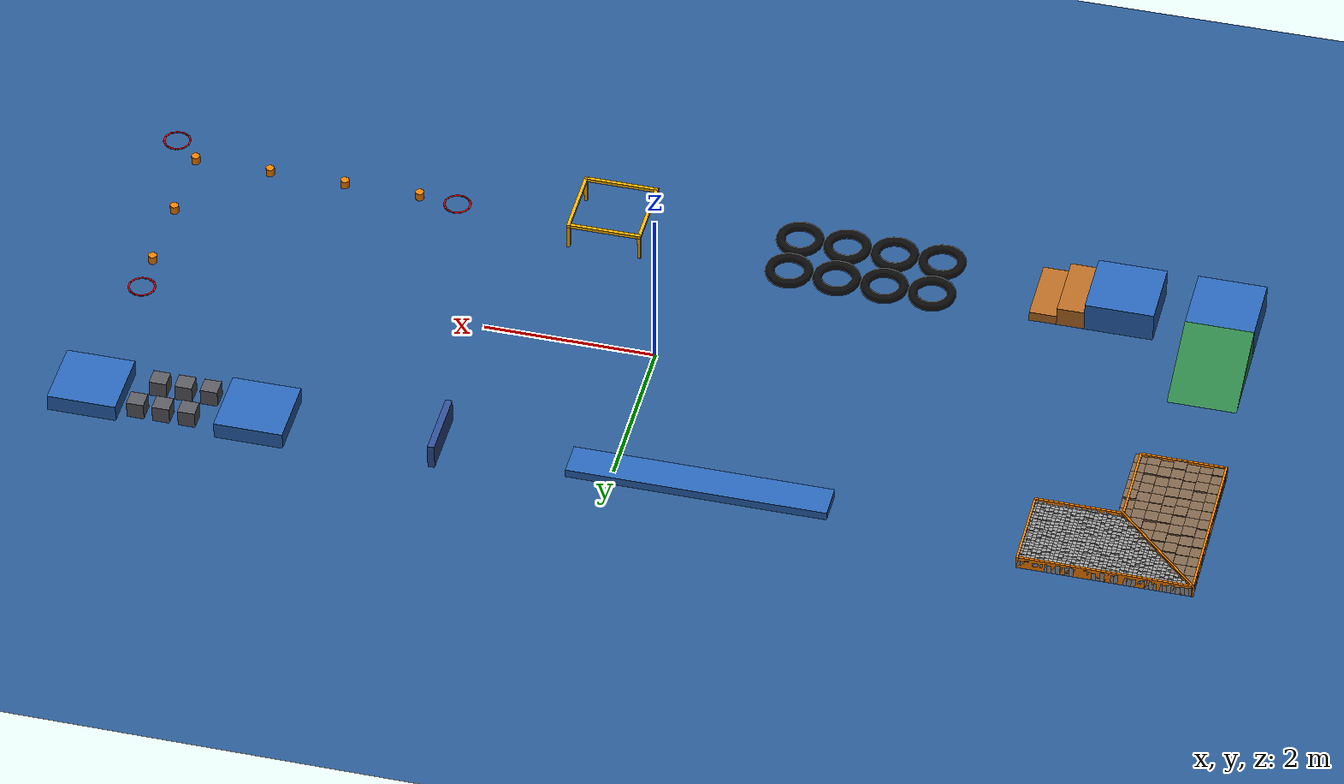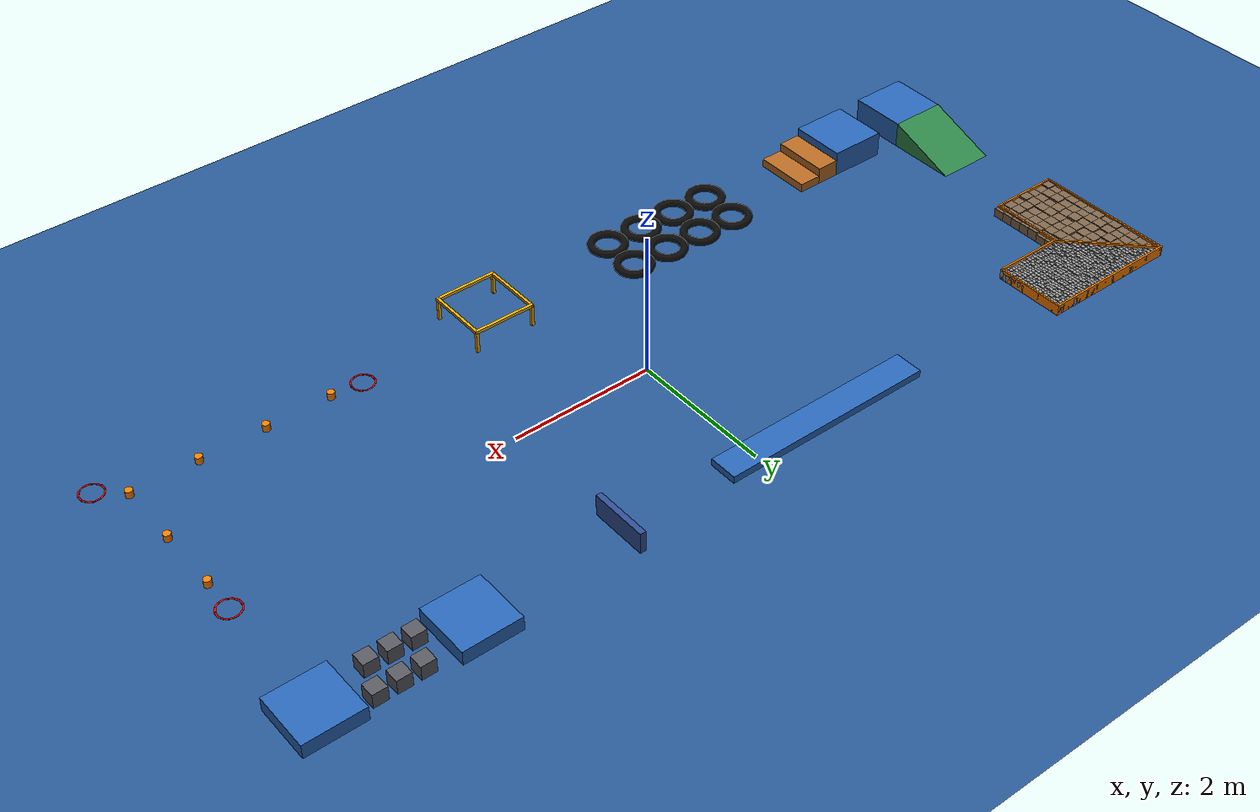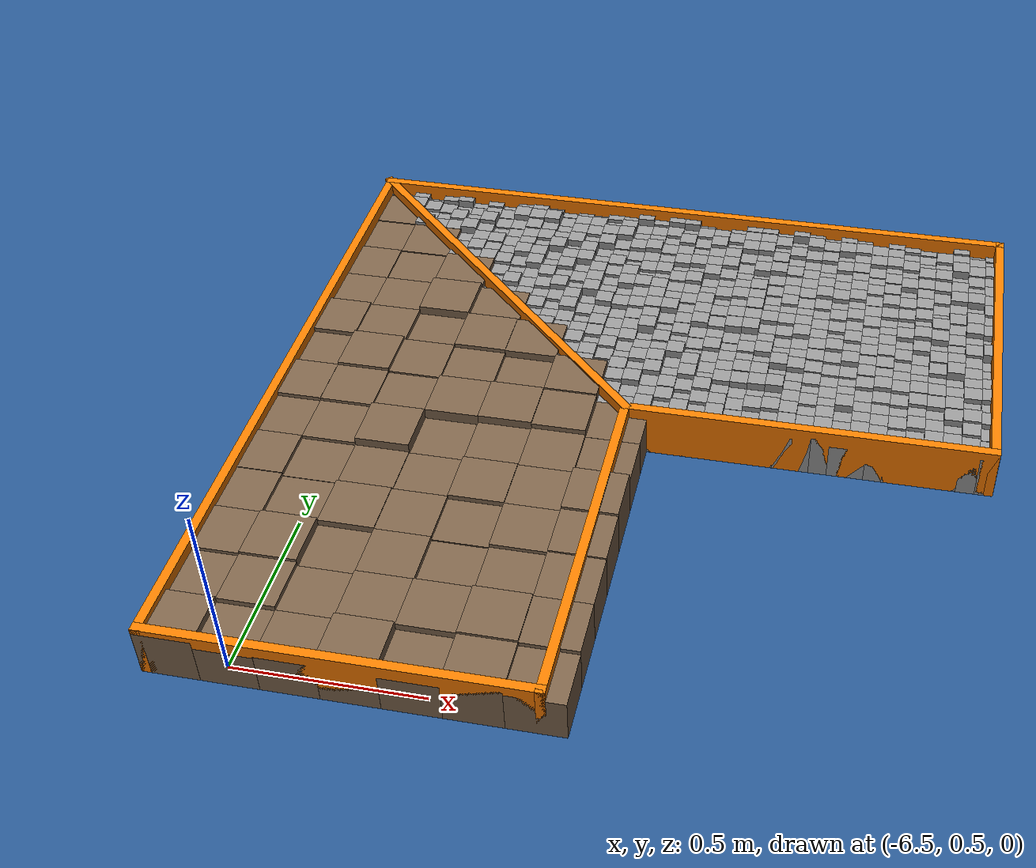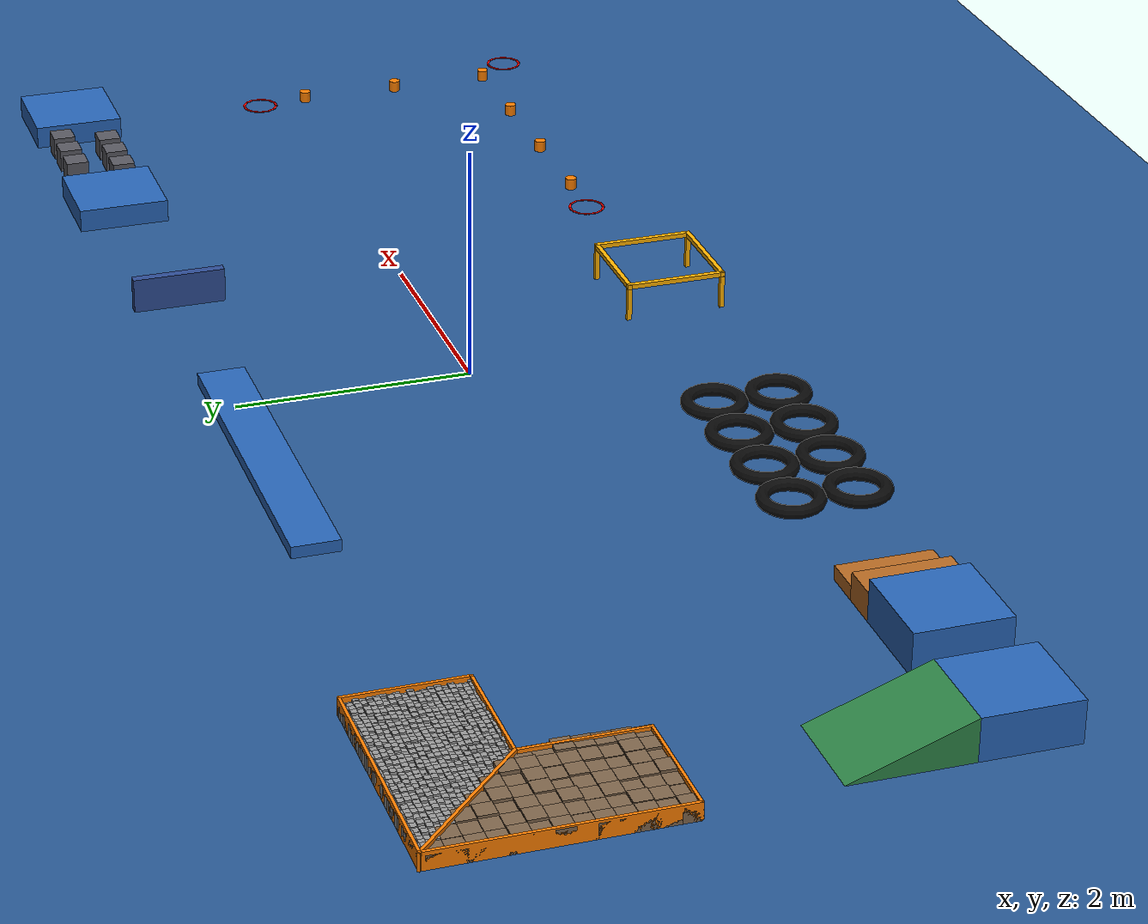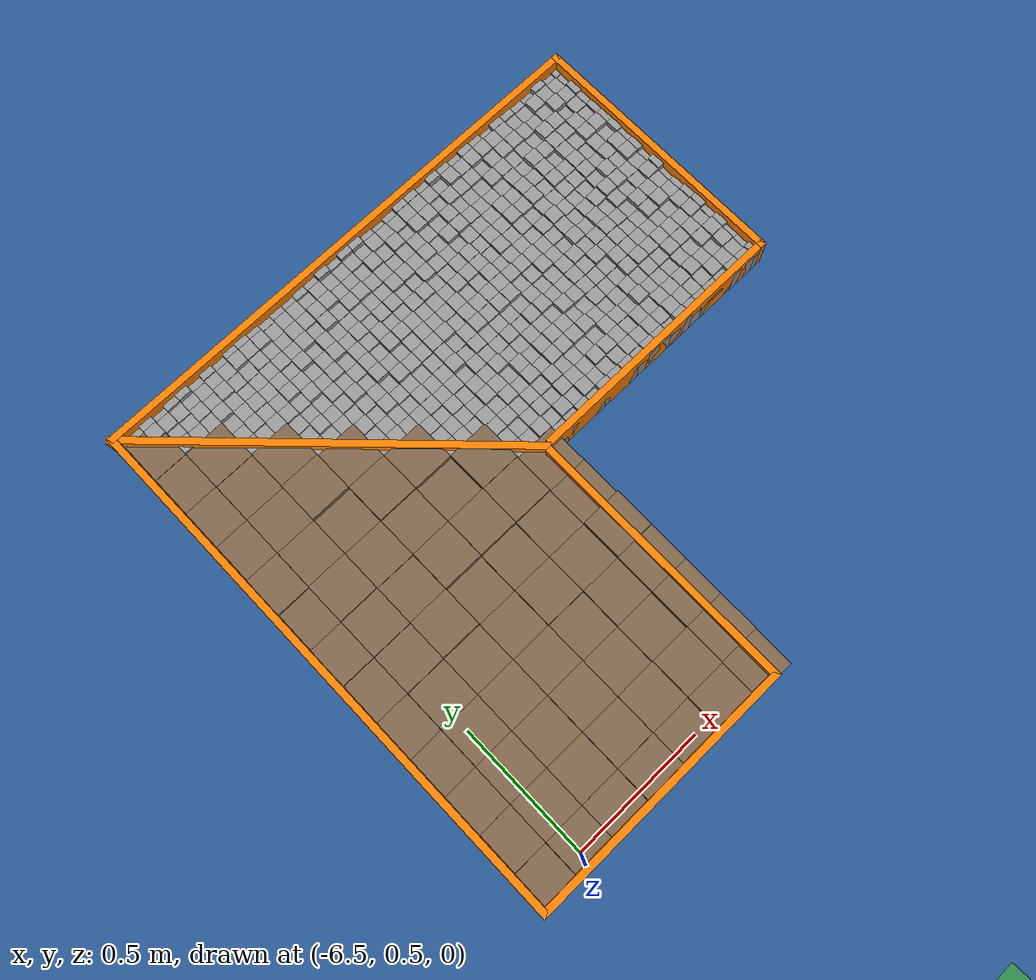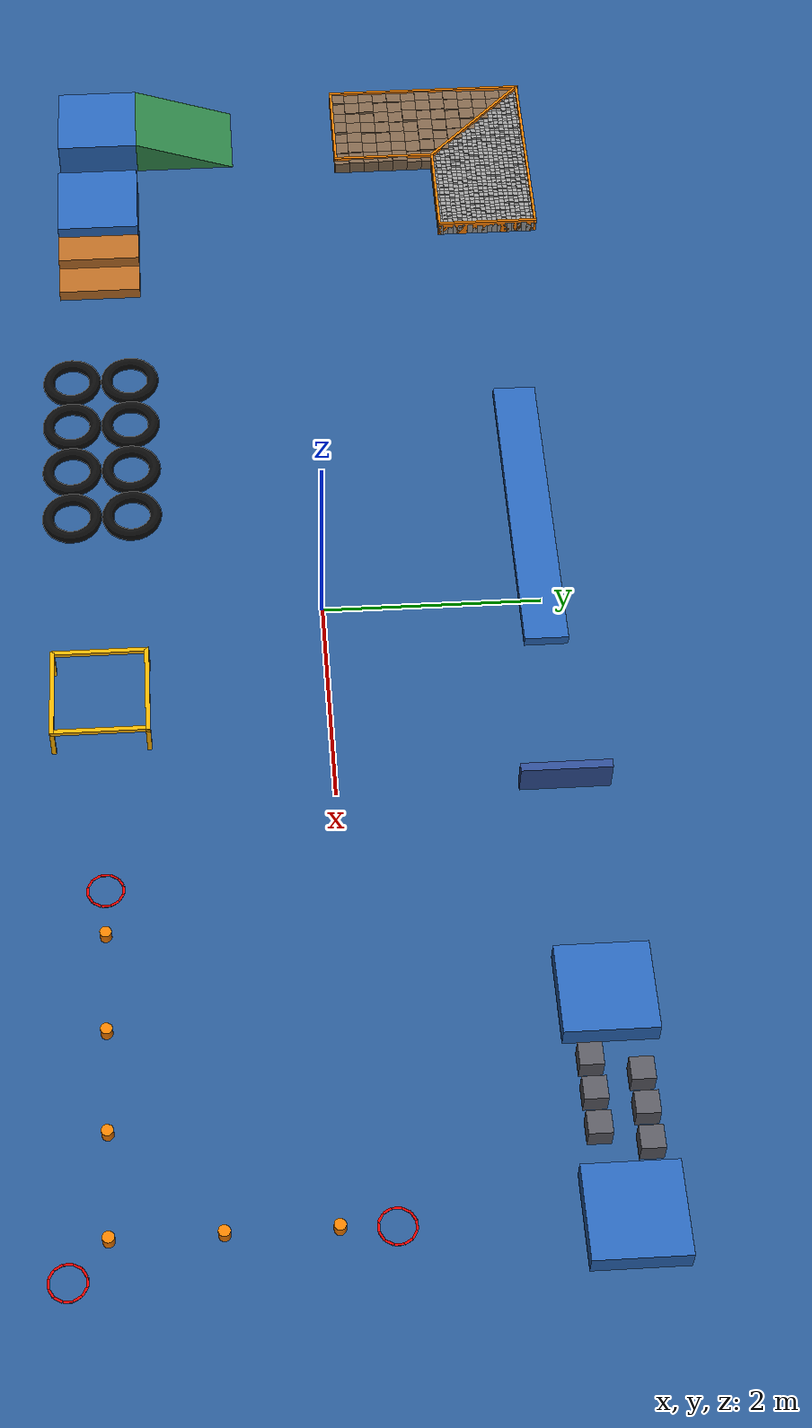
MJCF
<mujoco model="playground">
  <compiler angle="degree" coordinate="local" />
  <option gravity="0 0 -9.81" integrator="RK4" />
  <statistic center="0 0 0" extent="14.15" />
  <visual>
    <headlight diffuse="0.6 0.6 0.6" ambient="0.3 0.3 0.3" specular="0 0 0" />
    <rgba haze="0.15 0.25 0.35 1" />
    <global azimuth="-130" elevation="-20" />
    <map fogstart="15.565" fogend="50.94" />
  </visual>
  <asset>
    <texture name="skybox" type="skybox" builtin="gradient" rgb1="0.30 0.50 0.72" rgb2="0.015 0.035 0.09" width="512" height="3072" />
    <texture name="terrain_checker" type="2d" builtin="checker" mark="edge" rgb1="0.08 0.20 0.38" rgb2="0.24 0.50 0.78" markrgb="0.86 0.93 1.0" width="300" height="300" />
    <material name="terrain_material" texture="terrain_checker" texuniform="true" texrepeat="5 5" reflectance="0.15" />
    <hfield name="terrain" file="terrain.png" size="14.15 8.5 0.05 1e-6" />
    <mesh name="tire_ring_05_mesh" vertex="0.28 0 0 0.269496 0 0.0323282 0.241996 0 0.052308 0.208004 0 0.052308 0.180504 0 0.0323282 0.17 0 6.73555e-18 0.180504 0 -0.0323282 0.208004 0 -0.052308 0.241996 0 -0.052308 0.269496 0 -0.0323282 0.27045915 0.0724693616 0 0.260313157 0.0697506878 0.0323282 0.23375016 0.0626331241 0.052308 0.200916674 0.0538353233 0.052308 0.174353667 0.0467178484 0.0323282 0.164207122 0.0439993665 6.73555e-18 0.174353667 0.0467178484 -0.0323282 0.200916674 0.0538353233 -0.052308 0.23375016 0.0626331241 -0.052308 0.260313157 0.0697506878 -0.0323282 0.242487399 0.139999929 0 0.233390354 0.134748008 0.0323282 0.209574896 0.120997934 0.052308 0.180136865 0.104002038 0.052308 0.156320743 0.0902522493 0.0323282 0.147224303 0.0850000091 6.73555e-18 0.156320743 0.0902522493 -0.0323282 0.180136865 0.104002038 -0.052308 0.209574896 0.120997934 -0.052308 0.233390354 0.134748008 -0.0323282 0.197990013 0.197990013 0 0.190562513 0.190562513 0.0323282 0.171117013 0.171117013 0.052308 0.147081013 0.147081013 0.052308 0.127635663 0.127635663 0.0323282 0.120208163 0.120208163 6.73555e-18 0.127635663 0.127635663 -0.0323282 0.147081013 0.147081013 -0.052308 0.171117013 0.171117013 -0.052308 0.190562513 0.190562513 -0.0323282 0.139999929 0.242487399 0 0.134748008 0.233390354 0.0323282 0.120997934 0.209574896 0.052308 0.104002038 0.180136865 0.052308 0.0902522493 0.156320743 0.0323282 0.0850000091 0.147224303 6.73555e-18 0.0902522493 0.156320743 -0.0323282 0.104002038 0.180136865 -0.052308 0.120997934 0.209574896 -0.052308 0.134748008 0.233390354 -0.0323282 0.0724693616 0.27045915 0 0.0697506878 0.260313157 0.0323282 0.0626331241 0.23375016 0.052308 0.0538353233 0.200916674 0.052308 0.0467178484 0.174353667 0.0323282 0.0439993665 0.164207122 6.73555e-18 0.0467178484 0.174353667 -0.0323282 0.0538353233 0.200916674 -0.052308 0.0626331241 0.23375016 -0.052308 0.0697506878 0.260313157 -0.0323282 1.71450269e-17 0.28 0 1.65019008e-17 0.269496 0.0323282 1.48179942e-17 0.241996 0.052308 1.27366078e-17 0.208004 0.052308 1.10526981e-17 0.180504 0.0323282 1.04094991e-17 0.17 6.73555e-18 1.10526981e-17 0.180504 -0.0323282 1.27366078e-17 0.208004 -0.052308 1.48179942e-17 0.241996 -0.052308 1.65019008e-17 0.269496 -0.0323282 -0.0724693616 0.27045915 0 -0.0697506878 0.260313157 0.0323282 -0.0626331241 0.23375016 0.052308 -0.0538353233 0.200916674 0.052308 -0.0467178484 0.174353667 0.0323282 -0.0439993665 0.164207122 6.73555e-18 -0.0467178484 0.174353667 -0.0323282 -0.0538353233 0.200916674 -0.052308 -0.0626331241 0.23375016 -0.052308 -0.0697506878 0.260313157 -0.0323282 -0.139999929 0.242487399 0 -0.134748008 0.233390354 0.0323282 -0.120997934 0.209574896 0.052308 -0.104002038 0.180136865 0.052308 -0.0902522493 0.156320743 0.0323282 -0.0850000091 0.147224303 6.73555e-18 -0.0902522493 0.156320743 -0.0323282 -0.104002038 0.180136865 -0.052308 -0.120997934 0.209574896 -0.052308 -0.134748008 0.233390354 -0.0323282 -0.197990013 0.197990013 0 -0.190562513 0.190562513 0.0323282 -0.171117013 0.171117013 0.052308 -0.147081013 0.147081013 0.052308 -0.127635663 0.127635663 0.0323282 -0.120208163 0.120208163 6.73555e-18 -0.127635663 0.127635663 -0.0323282 -0.147081013 0.147081013 -0.052308 -0.171117013 0.171117013 -0.052308 -0.190562513 0.190562513 -0.0323282 -0.242487399 0.139999929 0 -0.233390354 0.134748008 0.0323282 -0.209574896 0.120997934 0.052308 -0.180136865 0.104002038 0.052308 -0.156320743 0.0902522493 0.0323282 -0.147224303 0.0850000091 6.73555e-18 -0.156320743 0.0902522493 -0.0323282 -0.180136865 0.104002038 -0.052308 -0.209574896 0.120997934 -0.052308 -0.233390354 0.134748008 -0.0323282 -0.27045915 0.0724693616 0 -0.260313157 0.0697506878 0.0323282 -0.23375016 0.0626331241 0.052308 -0.200916674 0.0538353233 0.052308 -0.174353667 0.0467178484 0.0323282 -0.164207122 0.0439993665 6.73555e-18 -0.174353667 0.0467178484 -0.0323282 -0.200916674 0.0538353233 -0.052308 -0.23375016 0.0626331241 -0.052308 -0.260313157 0.0697506878 -0.0323282 -0.28 3.42901373e-17 0 -0.269496 3.30037158e-17 0.0323282 -0.241996 2.96359885e-17 0.052308 -0.208004 2.54731067e-17 0.052308 -0.180504 2.21053962e-17 0.0323282 -0.17 2.08189391e-17 6.73555e-18 -0.180504 2.21053962e-17 -0.0323282 -0.208004 2.54731067e-17 -0.052308 -0.241996 2.96359885e-17 -0.052308 -0.269496 3.30037158e-17 -0.0323282 -0.27045915 -0.0724693616 0 -0.260313157 -0.0697506878 0.0323282 -0.23375016 -0.0626331241 0.052308 -0.200916674 -0.0538353233 0.052308 -0.174353667 -0.0467178484 0.0323282 -0.164207122 -0.0439993665 6.73555e-18 -0.174353667 -0.0467178484 -0.0323282 -0.200916674 -0.0538353233 -0.052308 -0.23375016 -0.0626331241 -0.052308 -0.260313157 -0.0697506878 -0.0323282 -0.242487399 -0.139999929 0 -0.233390354 -0.134748008 0.0323282 -0.209574896 -0.120997934 0.052308 -0.180136865 -0.104002038 0.052308 -0.156320743 -0.0902522493 0.0323282 -0.147224303 -0.0850000091 6.73555e-18 -0.156320743 -0.0902522493 -0.0323282 -0.180136865 -0.104002038 -0.052308 -0.209574896 -0.120997934 -0.052308 -0.233390354 -0.134748008 -0.0323282 -0.197990013 -0.197990013 0 -0.190562513 -0.190562513 0.0323282 -0.171117013 -0.171117013 0.052308 -0.147081013 -0.147081013 0.052308 -0.127635663 -0.127635663 0.0323282 -0.120208163 -0.120208163 6.73555e-18 -0.127635663 -0.127635663 -0.0323282 -0.147081013 -0.147081013 -0.052308 -0.171117013 -0.171117013 -0.052308 -0.190562513 -0.190562513 -0.0323282 -0.139999929 -0.242487399 0 -0.134748008 -0.233390354 0.0323282 -0.120997934 -0.209574896 0.052308 -0.104002038 -0.180136865 0.052308 -0.0902522493 -0.156320743 0.0323282 -0.0850000091 -0.147224303 6.73555e-18 -0.0902522493 -0.156320743 -0.0323282 -0.104002038 -0.180136865 -0.052308 -0.120997934 -0.209574896 -0.052308 -0.134748008 -0.233390354 -0.0323282 -0.0724693616 -0.27045915 0 -0.0697506878 -0.260313157 0.0323282 -0.0626331241 -0.23375016 0.052308 -0.0538353233 -0.200916674 0.052308 -0.0467178484 -0.174353667 0.0323282 -0.0439993665 -0.164207122 6.73555e-18 -0.0467178484 -0.174353667 -0.0323282 -0.0538353233 -0.200916674 -0.052308 -0.0626331241 -0.23375016 -0.052308 -0.0697506878 -0.260313157 -0.0323282 -5.14351642e-17 -0.28 0 -4.95056166e-17 -0.269496 0.0323282 -4.44538893e-17 -0.241996 0.052308 -3.82097145e-17 -0.208004 0.052308 -3.31580943e-17 -0.180504 0.0323282 -3.12285565e-17 -0.17 6.73555e-18 -3.31580943e-17 -0.180504 -0.0323282 -3.82097145e-17 -0.208004 -0.052308 -4.44538893e-17 -0.241996 -0.052308 -4.95056166e-17 -0.269496 -0.0323282 0.0724693616 -0.27045915 0 0.0697506878 -0.260313157 0.0323282 0.0626331241 -0.23375016 0.052308 0.0538353233 -0.200916674 0.052308 0.0467178484 -0.174353667 0.0323282 0.0439993665 -0.164207122 6.73555e-18 0.0467178484 -0.174353667 -0.0323282 0.0538353233 -0.200916674 -0.052308 0.0626331241 -0.23375016 -0.052308 0.0697506878 -0.260313157 -0.0323282 0.139999929 -0.242487399 0 0.134748008 -0.233390354 0.0323282 0.120997934 -0.209574896 0.052308 0.104002038 -0.180136865 0.052308 0.0902522493 -0.156320743 0.0323282 0.0850000091 -0.147224303 6.73555e-18 0.0902522493 -0.156320743 -0.0323282 0.104002038 -0.180136865 -0.052308 0.120997934 -0.209574896 -0.052308 0.134748008 -0.233390354 -0.0323282 0.197990013 -0.197990013 0 0.190562513 -0.190562513 0.0323282 0.171117013 -0.171117013 0.052308 0.147081013 -0.147081013 0.052308 0.127635663 -0.127635663 0.0323282 0.120208163 -0.120208163 6.73555e-18 0.127635663 -0.127635663 -0.0323282 0.147081013 -0.147081013 -0.052308 0.171117013 -0.171117013 -0.052308 0.190562513 -0.190562513 -0.0323282 0.242487399 -0.139999929 0 0.233390354 -0.134748008 0.0323282 0.209574896 -0.120997934 0.052308 0.180136865 -0.104002038 0.052308 0.156320743 -0.0902522493 0.0323282 0.147224303 -0.0850000091 6.73555e-18 0.156320743 -0.0902522493 -0.0323282 0.180136865 -0.104002038 -0.052308 0.209574896 -0.120997934 -0.052308 0.233390354 -0.134748008 -0.0323282 0.27045915 -0.0724693616 0 0.260313157 -0.0697506878 0.0323282 0.23375016 -0.0626331241 0.052308 0.200916674 -0.0538353233 0.052308 0.174353667 -0.0467178484 0.0323282 0.164207122 -0.0439993665 6.73555e-18 0.174353667 -0.0467178484 -0.0323282 0.200916674 -0.0538353233 -0.052308 0.23375016 -0.0626331241 -0.052308 0.260313157 -0.0697506878 -0.0323282" face="0 10 11 0 11 1 1 11 12 1 12 2 2 12 13 2 13 3 3 13 14 3 14 4 4 14 15 4 15 5 5 15 16 5 16 6 6 16 17 6 17 7 7 17 18 7 18 8 8 18 19 8 19 9 9 19 10 9 10 0 10 20 21 10 21 11 11 21 22 11 22 12 12 22 23 12 23 13 13 23 24 13 24 14 14 24 25 14 25 15 15 25 26 15 26 16 16 26 27 16 27 17 17 27 28 17 28 18 18 28 29 18 29 19 19 29 20 19 20 10 20 30 31 20 31 21 21 31 32 21 32 22 22 32 33 22 33 23 23 33 34 23 34 24 24 34 35 24 35 25 25 35 36 25 36 26 26 36 37 26 37 27 27 37 38 27 38 28 28 38 39 28 39 29 29 39 30 29 30 20 30 40 41 30 41 31 31 41 42 31 42 32 32 42 43 32 43 33 33 43 44 33 44 34 34 44 45 34 45 35 35 45 46 35 46 36 36 46 47 36 47 37 37 47 48 37 48 38 38 48 49 38 49 39 39 49 40 39 40 30 40 50 51 40 51 41 41 51 52 41 52 42 42 52 53 42 53 43 43 53 54 43 54 44 44 54 55 44 55 45 45 55 56 45 56 46 46 56 57 46 57 47 47 57 58 47 58 48 48 58 59 48 59 49 49 59 50 49 50 40 50 60 61 50 61 51 51 61 62 51 62 52 52 62 63 52 63 53 53 63 64 53 64 54 54 64 65 54 65 55 55 65 66 55 66 56 56 66 67 56 67 57 57 67 68 57 68 58 58 68 69 58 69 59 59 69 60 59 60 50 60 70 71 60 71 61 61 71 72 61 72 62 62 72 73 62 73 63 63 73 74 63 74 64 64 74 75 64 75 65 65 75 76 65 76 66 66 76 77 66 77 67 67 77 78 67 78 68 68 78 79 68 79 69 69 79 70 69 70 60 70 80 81 70 81 71 71 81 82 71 82 72 72 82 83 72 83 73 73 83 84 73 84 74 74 84 85 74 85 75 75 85 86 75 86 76 76 86 87 76 87 77 77 87 88 77 88 78 78 88 89 78 89 79 79 89 80 79 80 70 80 90 91 80 91 81 81 91 92 81 92 82 82 92 93 82 93 83 83 93 94 83 94 84 84 94 95 84 95 85 85 95 96 85 96 86 86 96 97 86 97 87 87 97 98 87 98 88 88 98 99 88 99 89 89 99 90 89 90 80 90 100 101 90 101 91 91 101 102 91 102 92 92 102 103 92 103 93 93 103 104 93 104 94 94 104 105 94 105 95 95 105 106 95 106 96 96 106 107 96 107 97 97 107 108 97 108 98 98 108 109 98 109 99 99 109 100 99 100 90 100 110 111 100 111 101 101 111 112 101 112 102 102 112 113 102 113 103 103 113 114 103 114 104 104 114 115 104 115 105 105 115 116 105 116 106 106 116 117 106 117 107 107 117 118 107 118 108 108 118 119 108 119 109 109 119 110 109 110 100 110 120 121 110 121 111 111 121 122 111 122 112 112 122 123 112 123 113 113 123 124 113 124 114 114 124 125 114 125 115 115 125 126 115 126 116 116 126 127 116 127 117 117 127 128 117 128 118 118 128 129 118 129 119 119 129 120 119 120 110 120 130 131 120 131 121 121 131 132 121 132 122 122 132 133 122 133 123 123 133 134 123 134 124 124 134 135 124 135 125 125 135 136 125 136 126 126 136 137 126 137 127 127 137 138 127 138 128 128 138 139 128 139 129 129 139 130 129 130 120 130 140 141 130 141 131 131 141 142 131 142 132 132 142 143 132 143 133 133 143 144 133 144 134 134 144 145 134 145 135 135 145 146 135 146 136 136 146 147 136 147 137 137 147 148 137 148 138 138 148 149 138 149 139 139 149 140 139 140 130 140 150 151 140 151 141 141 151 152 141 152 142 142 152 153 142 153 143 143 153 154 143 154 144 144 154 155 144 155 145 145 155 156 145 156 146 146 156 157 146 157 147 147 157 158 147 158 148 148 158 159 148 159 149 149 159 150 149 150 140 150 160 161 150 161 151 151 161 162 151 162 152 152 162 163 152 163 153 153 163 164 153 164 154 154 164 165 154 165 155 155 165 166 155 166 156 156 166 167 156 167 157 157 167 168 157 168 158 158 168 169 158 169 159 159 169 160 159 160 150 160 170 171 160 171 161 161 171 172 161 172 162 162 172 173 162 173 163 163 173 174 163 174 164 164 174 175 164 175 165 165 175 176 165 176 166 166 176 177 166 177 167 167 177 178 167 178 168 168 178 179 168 179 169 169 179 170 169 170 160 170 180 181 170 181 171 171 181 182 171 182 172 172 182 183 172 183 173 173 183 184 173 184 174 174 184 185 174 185 175 175 185 186 175 186 176 176 186 187 176 187 177 177 187 188 177 188 178 178 188 189 178 189 179 179 189 180 179 180 170 180 190 191 180 191 181 181 191 192 181 192 182 182 192 193 182 193 183 183 193 194 183 194 184 184 194 195 184 195 185 185 195 196 185 196 186 186 196 197 186 197 187 187 197 198 187 198 188 188 198 199 188 199 189 189 199 190 189 190 180 190 200 201 190 201 191 191 201 202 191 202 192 192 202 203 192 203 193 193 203 204 193 204 194 194 204 205 194 205 195 195 205 206 195 206 196 196 206 207 196 207 197 197 207 208 197 208 198 198 208 209 198 209 199 199 209 200 199 200 190 200 210 211 200 211 201 201 211 212 201 212 202 202 212 213 202 213 203 203 213 214 203 214 204 204 214 215 204 215 205 205 215 216 205 216 206 206 216 217 206 217 207 207 217 218 207 218 208 208 218 219 208 219 209 209 219 210 209 210 200 210 220 221 210 221 211 211 221 222 211 222 212 212 222 223 212 223 213 213 223 224 213 224 214 214 224 225 214 225 215 215 225 226 215 226 216 216 226 227 216 227 217 217 227 228 217 228 218 218 228 229 218 229 219 219 229 220 219 220 210 220 230 231 220 231 221 221 231 232 221 232 222 222 232 233 222 233 223 223 233 234 223 234 224 224 234 235 224 235 225 225 235 236 225 236 226 226 236 237 226 237 227 227 237 238 227 238 228 228 238 239 228 239 229 229 239 230 229 230 220 230 0 1 230 1 231 231 1 2 231 2 232 232 2 3 232 3 233 233 3 4 233 4 234 234 4 5 234 5 235 235 5 6 235 6 236 236 6 7 236 7 237 237 7 8 237 8 238 238 8 9 238 9 239 239 9 0 239 0 230" />
    <mesh name="tire_ring_06_mesh" vertex="0.28 0 0 0.269496 0 0.0323282 0.241996 0 0.052308 0.208004 0 0.052308 0.180504 0 0.0323282 0.17 0 6.73555e-18 0.180504 0 -0.0323282 0.208004 0 -0.052308 0.241996 0 -0.052308 0.269496 0 -0.0323282 0.27045915 0.0724693616 0 0.260313157 0.0697506878 0.0323282 0.23375016 0.0626331241 0.052308 0.200916674 0.0538353233 0.052308 0.174353667 0.0467178484 0.0323282 0.164207122 0.0439993665 6.73555e-18 0.174353667 0.0467178484 -0.0323282 0.200916674 0.0538353233 -0.052308 0.23375016 0.0626331241 -0.052308 0.260313157 0.0697506878 -0.0323282 0.242487399 0.139999929 0 0.233390354 0.134748008 0.0323282 0.209574896 0.120997934 0.052308 0.180136865 0.104002038 0.052308 0.156320743 0.0902522493 0.0323282 0.147224303 0.0850000091 6.73555e-18 0.156320743 0.0902522493 -0.0323282 0.180136865 0.104002038 -0.052308 0.209574896 0.120997934 -0.052308 0.233390354 0.134748008 -0.0323282 0.197990013 0.197990013 0 0.190562513 0.190562513 0.0323282 0.171117013 0.171117013 0.052308 0.147081013 0.147081013 0.052308 0.127635663 0.127635663 0.0323282 0.120208163 0.120208163 6.73555e-18 0.127635663 0.127635663 -0.0323282 0.147081013 0.147081013 -0.052308 0.171117013 0.171117013 -0.052308 0.190562513 0.190562513 -0.0323282 0.139999929 0.242487399 0 0.134748008 0.233390354 0.0323282 0.120997934 0.209574896 0.052308 0.104002038 0.180136865 0.052308 0.0902522493 0.156320743 0.0323282 0.0850000091 0.147224303 6.73555e-18 0.0902522493 0.156320743 -0.0323282 0.104002038 0.180136865 -0.052308 0.120997934 0.209574896 -0.052308 0.134748008 0.233390354 -0.0323282 0.0724693616 0.27045915 0 0.0697506878 0.260313157 0.0323282 0.0626331241 0.23375016 0.052308 0.0538353233 0.200916674 0.052308 0.0467178484 0.174353667 0.0323282 0.0439993665 0.164207122 6.73555e-18 0.0467178484 0.174353667 -0.0323282 0.0538353233 0.200916674 -0.052308 0.0626331241 0.23375016 -0.052308 0.0697506878 0.260313157 -0.0323282 1.71450269e-17 0.28 0 1.65019008e-17 0.269496 0.0323282 1.48179942e-17 0.241996 0.052308 1.27366078e-17 0.208004 0.052308 1.10526981e-17 0.180504 0.0323282 1.04094991e-17 0.17 6.73555e-18 1.10526981e-17 0.180504 -0.0323282 1.27366078e-17 0.208004 -0.052308 1.48179942e-17 0.241996 -0.052308 1.65019008e-17 0.269496 -0.0323282 -0.0724693616 0.27045915 0 -0.0697506878 0.260313157 0.0323282 -0.0626331241 0.23375016 0.052308 -0.0538353233 0.200916674 0.052308 -0.0467178484 0.174353667 0.0323282 -0.0439993665 0.164207122 6.73555e-18 -0.0467178484 0.174353667 -0.0323282 -0.0538353233 0.200916674 -0.052308 -0.0626331241 0.23375016 -0.052308 -0.0697506878 0.260313157 -0.0323282 -0.139999929 0.242487399 0 -0.134748008 0.233390354 0.0323282 -0.120997934 0.209574896 0.052308 -0.104002038 0.180136865 0.052308 -0.0902522493 0.156320743 0.0323282 -0.0850000091 0.147224303 6.73555e-18 -0.0902522493 0.156320743 -0.0323282 -0.104002038 0.180136865 -0.052308 -0.120997934 0.209574896 -0.052308 -0.134748008 0.233390354 -0.0323282 -0.197990013 0.197990013 0 -0.190562513 0.190562513 0.0323282 -0.171117013 0.171117013 0.052308 -0.147081013 0.147081013 0.052308 -0.127635663 0.127635663 0.0323282 -0.120208163 0.120208163 6.73555e-18 -0.127635663 0.127635663 -0.0323282 -0.147081013 0.147081013 -0.052308 -0.171117013 0.171117013 -0.052308 -0.190562513 0.190562513 -0.0323282 -0.242487399 0.139999929 0 -0.233390354 0.134748008 0.0323282 -0.209574896 0.120997934 0.052308 -0.180136865 0.104002038 0.052308 -0.156320743 0.0902522493 0.0323282 -0.147224303 0.0850000091 6.73555e-18 -0.156320743 0.0902522493 -0.0323282 -0.180136865 0.104002038 -0.052308 -0.209574896 0.120997934 -0.052308 -0.233390354 0.134748008 -0.0323282 -0.27045915 0.0724693616 0 -0.260313157 0.0697506878 0.0323282 -0.23375016 0.0626331241 0.052308 -0.200916674 0.0538353233 0.052308 -0.174353667 0.0467178484 0.0323282 -0.164207122 0.0439993665 6.73555e-18 -0.174353667 0.0467178484 -0.0323282 -0.200916674 0.0538353233 -0.052308 -0.23375016 0.0626331241 -0.052308 -0.260313157 0.0697506878 -0.0323282 -0.28 3.42901373e-17 0 -0.269496 3.30037158e-17 0.0323282 -0.241996 2.96359885e-17 0.052308 -0.208004 2.54731067e-17 0.052308 -0.180504 2.21053962e-17 0.0323282 -0.17 2.08189391e-17 6.73555e-18 -0.180504 2.21053962e-17 -0.0323282 -0.208004 2.54731067e-17 -0.052308 -0.241996 2.96359885e-17 -0.052308 -0.269496 3.30037158e-17 -0.0323282 -0.27045915 -0.0724693616 0 -0.260313157 -0.0697506878 0.0323282 -0.23375016 -0.0626331241 0.052308 -0.200916674 -0.0538353233 0.052308 -0.174353667 -0.0467178484 0.0323282 -0.164207122 -0.0439993665 6.73555e-18 -0.174353667 -0.0467178484 -0.0323282 -0.200916674 -0.0538353233 -0.052308 -0.23375016 -0.0626331241 -0.052308 -0.260313157 -0.0697506878 -0.0323282 -0.242487399 -0.139999929 0 -0.233390354 -0.134748008 0.0323282 -0.209574896 -0.120997934 0.052308 -0.180136865 -0.104002038 0.052308 -0.156320743 -0.0902522493 0.0323282 -0.147224303 -0.0850000091 6.73555e-18 -0.156320743 -0.0902522493 -0.0323282 -0.180136865 -0.104002038 -0.052308 -0.209574896 -0.120997934 -0.052308 -0.233390354 -0.134748008 -0.0323282 -0.197990013 -0.197990013 0 -0.190562513 -0.190562513 0.0323282 -0.171117013 -0.171117013 0.052308 -0.147081013 -0.147081013 0.052308 -0.127635663 -0.127635663 0.0323282 -0.120208163 -0.120208163 6.73555e-18 -0.127635663 -0.127635663 -0.0323282 -0.147081013 -0.147081013 -0.052308 -0.171117013 -0.171117013 -0.052308 -0.190562513 -0.190562513 -0.0323282 -0.139999929 -0.242487399 0 -0.134748008 -0.233390354 0.0323282 -0.120997934 -0.209574896 0.052308 -0.104002038 -0.180136865 0.052308 -0.0902522493 -0.156320743 0.0323282 -0.0850000091 -0.147224303 6.73555e-18 -0.0902522493 -0.156320743 -0.0323282 -0.104002038 -0.180136865 -0.052308 -0.120997934 -0.209574896 -0.052308 -0.134748008 -0.233390354 -0.0323282 -0.0724693616 -0.27045915 0 -0.0697506878 -0.260313157 0.0323282 -0.0626331241 -0.23375016 0.052308 -0.0538353233 -0.200916674 0.052308 -0.0467178484 -0.174353667 0.0323282 -0.0439993665 -0.164207122 6.73555e-18 -0.0467178484 -0.174353667 -0.0323282 -0.0538353233 -0.200916674 -0.052308 -0.0626331241 -0.23375016 -0.052308 -0.0697506878 -0.260313157 -0.0323282 -5.14351642e-17 -0.28 0 -4.95056166e-17 -0.269496 0.0323282 -4.44538893e-17 -0.241996 0.052308 -3.82097145e-17 -0.208004 0.052308 -3.31580943e-17 -0.180504 0.0323282 -3.12285565e-17 -0.17 6.73555e-18 -3.31580943e-17 -0.180504 -0.0323282 -3.82097145e-17 -0.208004 -0.052308 -4.44538893e-17 -0.241996 -0.052308 -4.95056166e-17 -0.269496 -0.0323282 0.0724693616 -0.27045915 0 0.0697506878 -0.260313157 0.0323282 0.0626331241 -0.23375016 0.052308 0.0538353233 -0.200916674 0.052308 0.0467178484 -0.174353667 0.0323282 0.0439993665 -0.164207122 6.73555e-18 0.0467178484 -0.174353667 -0.0323282 0.0538353233 -0.200916674 -0.052308 0.0626331241 -0.23375016 -0.052308 0.0697506878 -0.260313157 -0.0323282 0.139999929 -0.242487399 0 0.134748008 -0.233390354 0.0323282 0.120997934 -0.209574896 0.052308 0.104002038 -0.180136865 0.052308 0.0902522493 -0.156320743 0.0323282 0.0850000091 -0.147224303 6.73555e-18 0.0902522493 -0.156320743 -0.0323282 0.104002038 -0.180136865 -0.052308 0.120997934 -0.209574896 -0.052308 0.134748008 -0.233390354 -0.0323282 0.197990013 -0.197990013 0 0.190562513 -0.190562513 0.0323282 0.171117013 -0.171117013 0.052308 0.147081013 -0.147081013 0.052308 0.127635663 -0.127635663 0.0323282 0.120208163 -0.120208163 6.73555e-18 0.127635663 -0.127635663 -0.0323282 0.147081013 -0.147081013 -0.052308 0.171117013 -0.171117013 -0.052308 0.190562513 -0.190562513 -0.0323282 0.242487399 -0.139999929 0 0.233390354 -0.134748008 0.0323282 0.209574896 -0.120997934 0.052308 0.180136865 -0.104002038 0.052308 0.156320743 -0.0902522493 0.0323282 0.147224303 -0.0850000091 6.73555e-18 0.156320743 -0.0902522493 -0.0323282 0.180136865 -0.104002038 -0.052308 0.209574896 -0.120997934 -0.052308 0.233390354 -0.134748008 -0.0323282 0.27045915 -0.0724693616 0 0.260313157 -0.0697506878 0.0323282 0.23375016 -0.0626331241 0.052308 0.200916674 -0.0538353233 0.052308 0.174353667 -0.0467178484 0.0323282 0.164207122 -0.0439993665 6.73555e-18 0.174353667 -0.0467178484 -0.0323282 0.200916674 -0.0538353233 -0.052308 0.23375016 -0.0626331241 -0.052308 0.260313157 -0.0697506878 -0.0323282" face="0 10 11 0 11 1 1 11 12 1 12 2 2 12 13 2 13 3 3 13 14 3 14 4 4 14 15 4 15 5 5 15 16 5 16 6 6 16 17 6 17 7 7 17 18 7 18 8 8 18 19 8 19 9 9 19 10 9 10 0 10 20 21 10 21 11 11 21 22 11 22 12 12 22 23 12 23 13 13 23 24 13 24 14 14 24 25 14 25 15 15 25 26 15 26 16 16 26 27 16 27 17 17 27 28 17 28 18 18 28 29 18 29 19 19 29 20 19 20 10 20 30 31 20 31 21 21 31 32 21 32 22 22 32 33 22 33 23 23 33 34 23 34 24 24 34 35 24 35 25 25 35 36 25 36 26 26 36 37 26 37 27 27 37 38 27 38 28 28 38 39 28 39 29 29 39 30 29 30 20 30 40 41 30 41 31 31 41 42 31 42 32 32 42 43 32 43 33 33 43 44 33 44 34 34 44 45 34 45 35 35 45 46 35 46 36 36 46 47 36 47 37 37 47 48 37 48 38 38 48 49 38 49 39 39 49 40 39 40 30 40 50 51 40 51 41 41 51 52 41 52 42 42 52 53 42 53 43 43 53 54 43 54 44 44 54 55 44 55 45 45 55 56 45 56 46 46 56 57 46 57 47 47 57 58 47 58 48 48 58 59 48 59 49 49 59 50 49 50 40 50 60 61 50 61 51 51 61 62 51 62 52 52 62 63 52 63 53 53 63 64 53 64 54 54 64 65 54 65 55 55 65 66 55 66 56 56 66 67 56 67 57 57 67 68 57 68 58 58 68 69 58 69 59 59 69 60 59 60 50 60 70 71 60 71 61 61 71 72 61 72 62 62 72 73 62 73 63 63 73 74 63 74 64 64 74 75 64 75 65 65 75 76 65 76 66 66 76 77 66 77 67 67 77 78 67 78 68 68 78 79 68 79 69 69 79 70 69 70 60 70 80 81 70 81 71 71 81 82 71 82 72 72 82 83 72 83 73 73 83 84 73 84 74 74 84 85 74 85 75 75 85 86 75 86 76 76 86 87 76 87 77 77 87 88 77 88 78 78 88 89 78 89 79 79 89 80 79 80 70 80 90 91 80 91 81 81 91 92 81 92 82 82 92 93 82 93 83 83 93 94 83 94 84 84 94 95 84 95 85 85 95 96 85 96 86 86 96 97 86 97 87 87 97 98 87 98 88 88 98 99 88 99 89 89 99 90 89 90 80 90 100 101 90 101 91 91 101 102 91 102 92 92 102 103 92 103 93 93 103 104 93 104 94 94 104 105 94 105 95 95 105 106 95 106 96 96 106 107 96 107 97 97 107 108 97 108 98 98 108 109 98 109 99 99 109 100 99 100 90 100 110 111 100 111 101 101 111 112 101 112 102 102 112 113 102 113 103 103 113 114 103 114 104 104 114 115 104 115 105 105 115 116 105 116 106 106 116 117 106 117 107 107 117 118 107 118 108 108 118 119 108 119 109 109 119 110 109 110 100 110 120 121 110 121 111 111 121 122 111 122 112 112 122 123 112 123 113 113 123 124 113 124 114 114 124 125 114 125 115 115 125 126 115 126 116 116 126 127 116 127 117 117 127 128 117 128 118 118 128 129 118 129 119 119 129 120 119 120 110 120 130 131 120 131 121 121 131 132 121 132 122 122 132 133 122 133 123 123 133 134 123 134 124 124 134 135 124 135 125 125 135 136 125 136 126 126 136 137 126 137 127 127 137 138 127 138 128 128 138 139 128 139 129 129 139 130 129 130 120 130 140 141 130 141 131 131 141 142 131 142 132 132 142 143 132 143 133 133 143 144 133 144 134 134 144 145 134 145 135 135 145 146 135 146 136 136 146 147 136 147 137 137 147 148 137 148 138 138 148 149 138 149 139 139 149 140 139 140 130 140 150 151 140 151 141 141 151 152 141 152 142 142 152 153 142 153 143 143 153 154 143 154 144 144 154 155 144 155 145 145 155 156 145 156 146 146 156 157 146 157 147 147 157 158 147 158 148 148 158 159 148 159 149 149 159 150 149 150 140 150 160 161 150 161 151 151 161 162 151 162 152 152 162 163 152 163 153 153 163 164 153 164 154 154 164 165 154 165 155 155 165 166 155 166 156 156 166 167 156 167 157 157 167 168 157 168 158 158 168 169 158 169 159 159 169 160 159 160 150 160 170 171 160 171 161 161 171 172 161 172 162 162 172 173 162 173 163 163 173 174 163 174 164 164 174 175 164 175 165 165 175 176 165 176 166 166 176 177 166 177 167 167 177 178 167 178 168 168 178 179 168 179 169 169 179 170 169 170 160 170 180 181 170 181 171 171 181 182 171 182 172 172 182 183 172 183 173 173 183 184 173 184 174 174 184 185 174 185 175 175 185 186 175 186 176 176 186 187 176 187 177 177 187 188 177 188 178 178 188 189 178 189 179 179 189 180 179 180 170 180 190 191 180 191 181 181 191 192 181 192 182 182 192 193 182 193 183 183 193 194 183 194 184 184 194 195 184 195 185 185 195 196 185 196 186 186 196 197 186 197 187 187 197 198 187 198 188 188 198 199 188 199 189 189 199 190 189 190 180 190 200 201 190 201 191 191 201 202 191 202 192 192 202 203 192 203 193 193 203 204 193 204 194 194 204 205 194 205 195 195 205 206 195 206 196 196 206 207 196 207 197 197 207 208 197 208 198 198 208 209 198 209 199 199 209 200 199 200 190 200 210 211 200 211 201 201 211 212 201 212 202 202 212 213 202 213 203 203 213 214 203 214 204 204 214 215 204 215 205 205 215 216 205 216 206 206 216 217 206 217 207 207 217 218 207 218 208 208 218 219 208 219 209 209 219 210 209 210 200 210 220 221 210 221 211 211 221 222 211 222 212 212 222 223 212 223 213 213 223 224 213 224 214 214 224 225 214 225 215 215 225 226 215 226 216 216 226 227 216 227 217 217 227 228 217 228 218 218 228 229 218 229 219 219 229 220 219 220 210 220 230 231 220 231 221 221 231 232 221 232 222 222 232 233 222 233 223 223 233 234 223 234 224 224 234 235 224 235 225 225 235 236 225 236 226 226 236 237 226 237 227 227 237 238 227 238 228 228 238 239 228 239 229 229 239 230 229 230 220 230 0 1 230 1 231 231 1 2 231 2 232 232 2 3 232 3 233 233 3 4 233 4 234 234 4 5 234 5 235 235 5 6 235 6 236 236 6 7 236 7 237 237 7 8 237 8 238 238 8 9 238 9 239 239 9 0 239 0 230" />
    <mesh name="ramp_10_mesh" vertex="-0.4945 -0.4 0 0.4945 -0.4 0 0.4945 -0.4 0.36 -0.4945 0.4 0 0.4945 0.4 0 0.4945 0.4 0.36" face="0 4 1 0 3 4 0 1 2 3 5 4 1 5 2 1 4 5 0 2 5 0 5 3" />
  </asset>
    <worldbody>
    <light pos="0 0 8" directional="true" dir="0 0 -1" />
    <geom name="ground" type="plane" size="0 0 0.05" material="terrain_material" contype="1" conaffinity="1" />
    <geom name="high_wall_00" type="box" size="0.4 0.04 0.15" rgba="0.18 0.30 0.58 1" friction="0.8 0.1 0.1" pos="2 2 0.15" euler="0 0 90" />
    <geom name="stepping_stones_01_00" type="box" size="0.1 0.1 0.1" rgba="0.35 0.35 0.38 1" friction="0.8 0.1 0.1" pos="4.70 1.9 0.1" />
    <geom name="stepping_stones_01_01" type="box" size="0.1 0.1 0.1" rgba="0.35 0.35 0.38 1" friction="0.8 0.1 0.1" pos="5.00 1.9 0.1" />
    <geom name="stepping_stones_01_02" type="box" size="0.1 0.1 0.1" rgba="0.35 0.35 0.38 1" friction="0.8 0.1 0.1" pos="5.30 1.9 0.1" />
    <geom name="stepping_stones_01_03" type="box" size="0.1 0.1 0.1" rgba="0.35 0.35 0.38 1" friction="0.8 0.1 0.1" pos="4.85 2.3 0.1" />
    <geom name="stepping_stones_01_04" type="box" size="0.1 0.1 0.1" rgba="0.35 0.35 0.38 1" friction="0.8 0.1 0.1" pos="5.15 2.3 0.1" />
    <geom name="stepping_stones_01_05" type="box" size="0.1 0.1 0.1" rgba="0.35 0.35 0.38 1" friction="0.8 0.1 0.1" pos="5.45 2.3 0.1" />
    <geom name="platform_02" type="box" size="0.4 0.4 0.1" rgba="0.16 0.40 0.72 1" friction="0.8 0.1 0.1" pos="6.05 2.1 0.1" />
    <geom name="platform_03" type="box" size="0.4 0.4 0.1" rgba="0.16 0.40 0.72 1" friction="0.8 0.1 0.1" pos="4.10 2.1 0.1" />
    <geom name="platform_04" type="box" size="1.5 0.2 0.05" rgba="0.16 0.40 0.72 1" friction="0.8 0.1 0.1" pos="-1 2 0.05" />
    <geom name="tire_ring_05_00" type="mesh" mesh="tire_ring_05_mesh" rgba="0.04 0.04 0.04 1" friction="0.8 0.1 0.1" pos="-2.84 -1.72 0.055" />
    <geom name="tire_ring_05_01" type="mesh" mesh="tire_ring_05_mesh" rgba="0.04 0.04 0.04 1" friction="0.8 0.1 0.1" pos="-2.28 -1.72 0.055" />
    <geom name="tire_ring_05_02" type="mesh" mesh="tire_ring_05_mesh" rgba="0.04 0.04 0.04 1" friction="0.8 0.1 0.1" pos="-1.72 -1.72 0.055" />
    <geom name="tire_ring_05_03" type="mesh" mesh="tire_ring_05_mesh" rgba="0.04 0.04 0.04 1" friction="0.8 0.1 0.1" pos="-1.16 -1.72 0.055" />
    <geom name="tire_ring_06_00" type="mesh" mesh="tire_ring_06_mesh" rgba="0.04 0.04 0.04 1" friction="0.8 0.1 0.1" pos="-2.84 -2.28 0.055" />
    <geom name="tire_ring_06_01" type="mesh" mesh="tire_ring_06_mesh" rgba="0.04 0.04 0.04 1" friction="0.8 0.1 0.1" pos="-2.28 -2.28 0.055" />
    <geom name="tire_ring_06_02" type="mesh" mesh="tire_ring_06_mesh" rgba="0.04 0.04 0.04 1" friction="0.8 0.1 0.1" pos="-1.72 -2.28 0.055" />
    <geom name="tire_ring_06_03" type="mesh" mesh="tire_ring_06_mesh" rgba="0.04 0.04 0.04 1" friction="0.8 0.1 0.1" pos="-1.16 -2.28 0.055" />
    <geom name="stairs_07_00" type="box" size="0.16 0.4 0.06" rgba="0.72 0.42 0.14 1" friction="0.8 0.1 0.1" pos="-4.16 -2 0.06" euler="0 0 180" />
    <geom name="stairs_07_01" type="box" size="0.16 0.4 0.12" rgba="0.72 0.42 0.14 1" friction="0.8 0.1 0.1" pos="-4.48 -2 0.12" euler="0 0 180" />
    <geom name="platform_08" type="box" size="0.4 0.4 0.18" rgba="0.16 0.40 0.72 1" friction="0.8 0.1 0.1" pos="-5.04 -2 0.18" />
    <geom name="platform_09" type="box" size="0.4 0.4 0.18" rgba="0.16 0.40 0.72 1" friction="0.8 0.1 0.1" pos="-6.20 -2 0.18" />
    <geom name="ramp_10" type="mesh" mesh="ramp_10_mesh" rgba="0.18 0.52 0.28 1" friction="0.8 0.1 0.1" pos="-6.20 -1.1055 0" euler="0 0 270" />
<!-- ===== 限高框架：内高 290mm，内宽 800mm，内长 800mm ===== -->
<!-- 4 根竖直立柱 -->
<geom name="limit_frame_pillar_0" type="box" size="0.02 0.02 0.145" pos="1.42  -1.6 0.145" rgba="1.0 0.7 0.0 1" friction="0.8 0.1 0.1"/>
<geom name="limit_frame_pillar_1" type="box" size="0.02 0.02 0.145" pos="0.58  -1.6 0.145" rgba="1.0 0.7 0.0 1" friction="0.8 0.1 0.1"/>
<geom name="limit_frame_pillar_2" type="box" size="0.02 0.02 0.145" pos="1.42 -2.44 0.145" rgba="1.0 0.7 0.0 1" friction="0.8 0.1 0.1"/>
<geom name="limit_frame_pillar_3" type="box" size="0.02 0.02 0.145" pos="0.58 -2.44 0.145" rgba="1.0 0.7 0.0 1" friction="0.8 0.1 0.1"/>
<!-- 4 根顶部横梁 -->
<geom name="limit_frame_beam_x0" type="box" size="0.44 0.02 0.02" pos="1.00  -1.6 0.31" rgba="1.0 0.7 0.0 1" friction="0.8 0.1 0.1"/>
<geom name="limit_frame_beam_x1" type="box" size="0.44 0.02 0.02" pos="1.00  -2.44 0.31" rgba="1.0 0.7 0.0 1" friction="0.8 0.1 0.1"/>
<geom name="limit_frame_beam_y0" type="box" size="0.02 0.44 0.02" pos="1.42  -2.02 0.31" rgba="1.0 0.7 0.0 1" friction="0.8 0.1 0.1"/>
<geom name="limit_frame_beam_y1" type="box" size="0.02 0.44 0.02" pos="0.58  -2.02 0.31" rgba="1.0 0.7 0.0 1" friction="0.8 0.1 0.1"/>
    <!-- ===== 镜像 L 形绕桩区（整体偏移 +6.0, -2.0） ===== -->
    <!-- 水平向 -X 共 4 桩，竖直向 +Y 额外 2 桩，总 6 桩 -->
    <!-- 桩径 100mm，桩高 100mm，中心距 900mm -->
    <geom name="L_pile_corner" type="cylinder" pos=" 6.0 -2.0 0.05" size="0.05 0.05" rgba="1.0 0.5 0.0 1" friction="0.8 0.1 0.1"/>
    <geom name="L_pile_negX1" type="cylinder" pos=" 5.1 -2.0 0.05" size="0.05 0.05" rgba="1.0 0.5 0.0 1" friction="0.8 0.1 0.1"/>
    <geom name="L_pile_negX2" type="cylinder" pos=" 4.2 -2.0 0.05" size="0.05 0.05" rgba="1.0 0.5 0.0 1" friction="0.8 0.1 0.1"/>
    <geom name="L_pile_negX3" type="cylinder" pos=" 3.3 -2.0 0.05" size="0.05 0.05" rgba="1.0 0.5 0.0 1" friction="0.8 0.1 0.1"/>
    <geom name="L_pile_posY1" type="cylinder" pos=" 6.0 -1.1 0.05" size="0.05 0.05" rgba="1.0 0.5 0.0 1" friction="0.8 0.1 0.1"/>
    <geom name="L_pile_posY2" type="cylinder" pos=" 6.0 -0.2 0.05" size="0.05 0.05" rgba="1.0 0.5 0.0 1" friction="0.8 0.1 0.1"/>

    <!-- ===== 必达区 A：水平端外侧，中心 (2.85, -2.0)，直径 300mm 红色虚线圆 ===== -->
    <geom name="L_reach_A_00" type="box" pos=" 3.0000 -2.0000 0.0020" size="0.0388 0.0100 0.0020" euler="0 0  90.00" rgba="1 0 0 1"/>
    <geom name="L_reach_A_01" type="box" pos=" 2.9799 -1.9250 0.0020" size="0.0388 0.0100 0.0020" euler="0 0 120.00" rgba="1 0 0 1"/>
    <geom name="L_reach_A_02" type="box" pos=" 2.9250 -1.8701 0.0020" size="0.0388 0.0100 0.0020" euler="0 0 150.00" rgba="1 0 0 1"/>
    <geom name="L_reach_A_03" type="box" pos=" 2.8500 -1.8500 0.0020" size="0.0388 0.0100 0.0020" euler="0 0 180.00" rgba="1 0 0 1"/>
    <geom name="L_reach_A_04" type="box" pos=" 2.7750 -1.8701 0.0020" size="0.0388 0.0100 0.0020" euler="0 0 210.00" rgba="1 0 0 1"/>
    <geom name="L_reach_A_05" type="box" pos=" 2.7201 -1.9250 0.0020" size="0.0388 0.0100 0.0020" euler="0 0 240.00" rgba="1 0 0 1"/>
    <geom name="L_reach_A_06" type="box" pos=" 2.7000 -2.0000 0.0020" size="0.0388 0.0100 0.0020" euler="0 0 270.00" rgba="1 0 0 1"/>
    <geom name="L_reach_A_07" type="box" pos=" 2.7201 -2.0750 0.0020" size="0.0388 0.0100 0.0020" euler="0 0 300.00" rgba="1 0 0 1"/>
    <geom name="L_reach_A_08" type="box" pos=" 2.7750 -2.1299 0.0020" size="0.0388 0.0100 0.0020" euler="0 0 330.00" rgba="1 0 0 1"/>
    <geom name="L_reach_A_09" type="box" pos=" 2.8500 -2.1500 0.0020" size="0.0388 0.0100 0.0020" euler="0 0 360.00" rgba="1 0 0 1"/>
    <geom name="L_reach_A_10" type="box" pos=" 2.9250 -2.1299 0.0020" size="0.0388 0.0100 0.0020" euler="0 0 390.00" rgba="1 0 0 1"/>
    <geom name="L_reach_A_11" type="box" pos=" 2.9799 -2.0750 0.0020" size="0.0388 0.0100 0.0020" euler="0 0 420.00" rgba="1 0 0 1"/>

    <!-- ===== 必达区 B：竖直端外侧，中心 (6.0, 0.25)，直径 300mm 红色虚线圆 ===== -->
    <geom name="L_reach_B_00" type="box" pos=" 6.1500  0.2500 0.0020" size="0.0388 0.0100 0.0020" euler="0 0  90.00" rgba="1 0 0 1"/>
    <geom name="L_reach_B_01" type="box" pos=" 6.1299  0.3250 0.0020" size="0.0388 0.0100 0.0020" euler="0 0 120.00" rgba="1 0 0 1"/>
    <geom name="L_reach_B_02" type="box" pos=" 6.0750  0.3799 0.0020" size="0.0388 0.0100 0.0020" euler="0 0 150.00" rgba="1 0 0 1"/>
    <geom name="L_reach_B_03" type="box" pos=" 6.0000  0.4000 0.0020" size="0.0388 0.0100 0.0020" euler="0 0 180.00" rgba="1 0 0 1"/>
    <geom name="L_reach_B_04" type="box" pos=" 5.9250  0.3799 0.0020" size="0.0388 0.0100 0.0020" euler="0 0 210.00" rgba="1 0 0 1"/>
    <geom name="L_reach_B_05" type="box" pos=" 5.8701  0.3250 0.0020" size="0.0388 0.0100 0.0020" euler="0 0 240.00" rgba="1 0 0 1"/>
    <geom name="L_reach_B_06" type="box" pos=" 5.8500  0.2500 0.0020" size="0.0388 0.0100 0.0020" euler="0 0 270.00" rgba="1 0 0 1"/>
    <geom name="L_reach_B_07" type="box" pos=" 5.8701  0.1750 0.0020" size="0.0388 0.0100 0.0020" euler="0 0 300.00" rgba="1 0 0 1"/>
    <geom name="L_reach_B_08" type="box" pos=" 5.9250  0.1201 0.0020" size="0.0388 0.0100 0.0020" euler="0 0 330.00" rgba="1 0 0 1"/>
    <geom name="L_reach_B_09" type="box" pos=" 6.0000  0.1000 0.0020" size="0.0388 0.0100 0.0020" euler="0 0 360.00" rgba="1 0 0 1"/>
    <geom name="L_reach_B_10" type="box" pos=" 6.0750  0.1201 0.0020" size="0.0388 0.0100 0.0020" euler="0 0 390.00" rgba="1 0 0 1"/>
    <geom name="L_reach_B_11" type="box" pos=" 6.1299  0.1750 0.0020" size="0.0388 0.0100 0.0020" euler="0 0 420.00" rgba="1 0 0 1"/>

    <!-- ===== 必达区 C：拐角外侧，中心 (6.3182, -2.3182)，直径 300mm 红色虚线圆 ===== -->
    <geom name="L_reach_C_00" type="box" pos=" 6.4682 -2.3182 0.0020" size="0.0388 0.0100 0.0020" euler="0 0  90.00" rgba="1 0 0 1"/>
    <geom name="L_reach_C_01" type="box" pos=" 6.4481 -2.2432 0.0020" size="0.0388 0.0100 0.0020" euler="0 0 120.00" rgba="1 0 0 1"/>
    <geom name="L_reach_C_02" type="box" pos=" 6.3932 -2.1883 0.0020" size="0.0388 0.0100 0.0020" euler="0 0 150.00" rgba="1 0 0 1"/>
    <geom name="L_reach_C_03" type="box" pos=" 6.3182 -2.1682 0.0020" size="0.0388 0.0100 0.0020" euler="0 0 180.00" rgba="1 0 0 1"/>
    <geom name="L_reach_C_04" type="box" pos=" 6.2432 -2.1883 0.0020" size="0.0388 0.0100 0.0020" euler="0 0 210.00" rgba="1 0 0 1"/>
    <geom name="L_reach_C_05" type="box" pos=" 6.1883 -2.2432 0.0020" size="0.0388 0.0100 0.0020" euler="0 0 240.00" rgba="1 0 0 1"/>
    <geom name="L_reach_C_06" type="box" pos=" 6.1682 -2.3182 0.0020" size="0.0388 0.0100 0.0020" euler="0 0 270.00" rgba="1 0 0 1"/>
    <geom name="L_reach_C_07" type="box" pos=" 6.1883 -2.3932 0.0020" size="0.0388 0.0100 0.0020" euler="0 0 300.00" rgba="1 0 0 1"/>
    <geom name="L_reach_C_08" type="box" pos=" 6.2432 -2.4481 0.0020" size="0.0388 0.0100 0.0020" euler="0 0 330.00" rgba="1 0 0 1"/>
    <geom name="L_reach_C_09" type="box" pos=" 6.3182 -2.4682 0.0020" size="0.0388 0.0100 0.0020" euler="0 0 360.00" rgba="1 0 0 1"/>
    <geom name="L_reach_C_10" type="box" pos=" 6.3932 -2.4481 0.0020" size="0.0388 0.0100 0.0020" euler="0 0 390.00" rgba="1 0 0 1"/>
    <geom name="L_reach_C_11" type="box" pos=" 6.4481 -2.3932 0.0020" size="0.0388 0.0100 0.0020" euler="0 0 420.00" rgba="1 0 0 1"/>
<geom name="pit_wall_left" type="box" pos="-6.6875 1.4500 0.0750" size="0.0125 1.0000 0.0750" rgba="1.0 0.5 0.0 1"/>
<geom name="pit_wall_top" type="box" pos="-5.7000 2.4375 0.0750" size="1.0000 0.0125 0.0750" rgba="1.0 0.5 0.0 1"/>
<geom name="pit_wall_right_top" type="box" pos="-4.7125 1.9500 0.0750" size="0.0125 0.5000 0.0750" rgba="1.0 0.5 0.0 1"/>
<geom name="pit_wall_inner" type="box" pos="-5.2000 1.4625 0.0750" size="0.5000 0.0125 0.0750" rgba="1.0 0.5 0.0 1"/>
<geom name="pit_wall_right_bot" type="box" pos="-5.7125 0.9500 0.0750" size="0.0125 0.5000 0.0750" rgba="1.0 0.5 0.0 1"/>
<geom name="pit_wall_bot" type="box" pos="-6.2000 0.4625 0.0750" size="0.5000 0.0125 0.0750" rgba="1.0 0.5 0.0 1"/>
<geom name="pit_separator" type="box" pos="-6.2000 1.9500 0.0750" size="0.7071 0.0125 0.0750" euler="0 0 -45.00" rgba="1.0 0.5 0.0 1"/>
<geom name="gravel_500_5400" type="box" pos="-6.6750 2.4250 0.0596" size="0.0250 0.0250 0.0596" rgba="0.6 0.6 0.6 1"/>
<geom name="gravel_550_5350" type="box" pos="-6.6250 2.3750 0.0504" size="0.0250 0.0250 0.0504" rgba="0.6 0.6 0.6 1"/>
<geom name="gravel_550_5400" type="box" pos="-6.6250 2.4250 0.0541" size="0.0250 0.0250 0.0541" rgba="0.6 0.6 0.6 1"/>
<geom name="gravel_600_5300" type="box" pos="-6.5750 2.3250 0.0533" size="0.0250 0.0250 0.0533" rgba="0.6 0.6 0.6 1"/>
<geom name="gravel_600_5350" type="box" pos="-6.5750 2.3750 0.0610" size="0.0250 0.0250 0.0610" rgba="0.6 0.6 0.6 1"/>
<geom name="gravel_600_5400" type="box" pos="-6.5750 2.4250 0.0602" size="0.0250 0.0250 0.0602" rgba="0.6 0.6 0.6 1"/>
<geom name="gravel_650_5250" type="box" pos="-6.5250 2.2750 0.0634" size="0.0250 0.0250 0.0634" rgba="0.6 0.6 0.6 1"/>
<geom name="gravel_650_5300" type="box" pos="-6.5250 2.3250 0.0513" size="0.0250 0.0250 0.0513" rgba="0.6 0.6 0.6 1"/>
<geom name="gravel_650_5350" type="box" pos="-6.5250 2.3750 0.0563" size="0.0250 0.0250 0.0563" rgba="0.6 0.6 0.6 1"/>
<geom name="gravel_650_5400" type="box" pos="-6.5250 2.4250 0.0504" size="0.0250 0.0250 0.0504" rgba="0.6 0.6 0.6 1"/>
<geom name="gravel_700_5200" type="box" pos="-6.4750 2.2250 0.0533" size="0.0250 0.0250 0.0533" rgba="0.6 0.6 0.6 1"/>
<geom name="gravel_700_5250" type="box" pos="-6.4750 2.2750 0.0576" size="0.0250 0.0250 0.0576" rgba="0.6 0.6 0.6 1"/>
<geom name="gravel_700_5300" type="box" pos="-6.4750 2.3250 0.0504" size="0.0250 0.0250 0.0504" rgba="0.6 0.6 0.6 1"/>
<geom name="gravel_700_5350" type="box" pos="-6.4750 2.3750 0.0530" size="0.0250 0.0250 0.0530" rgba="0.6 0.6 0.6 1"/>
<geom name="gravel_700_5400" type="box" pos="-6.4750 2.4250 0.0597" size="0.0250 0.0250 0.0597" rgba="0.6 0.6 0.6 1"/>
<geom name="gravel_750_5150" type="box" pos="-6.4250 2.1750 0.0582" size="0.0250 0.0250 0.0582" rgba="0.6 0.6 0.6 1"/>
<geom name="gravel_750_5200" type="box" pos="-6.4250 2.2250 0.0533" size="0.0250 0.0250 0.0533" rgba="0.6 0.6 0.6 1"/>
<geom name="gravel_750_5250" type="box" pos="-6.4250 2.2750 0.0588" size="0.0250 0.0250 0.0588" rgba="0.6 0.6 0.6 1"/>
<geom name="gravel_750_5300" type="box" pos="-6.4250 2.3250 0.0621" size="0.0250 0.0250 0.0621" rgba="0.6 0.6 0.6 1"/>
<geom name="gravel_750_5350" type="box" pos="-6.4250 2.3750 0.0501" size="0.0250 0.0250 0.0501" rgba="0.6 0.6 0.6 1"/>
<geom name="gravel_750_5400" type="box" pos="-6.4250 2.4250 0.0621" size="0.0250 0.0250 0.0621" rgba="0.6 0.6 0.6 1"/>
<geom name="gravel_800_5100" type="box" pos="-6.3750 2.1250 0.0605" size="0.0250 0.0250 0.0605" rgba="0.6 0.6 0.6 1"/>
<geom name="gravel_800_5150" type="box" pos="-6.3750 2.1750 0.0551" size="0.0250 0.0250 0.0551" rgba="0.6 0.6 0.6 1"/>
<geom name="gravel_800_5200" type="box" pos="-6.3750 2.2250 0.0523" size="0.0250 0.0250 0.0523" rgba="0.6 0.6 0.6 1"/>
<geom name="gravel_800_5250" type="box" pos="-6.3750 2.2750 0.0644" size="0.0250 0.0250 0.0644" rgba="0.6 0.6 0.6 1"/>
<geom name="gravel_800_5300" type="box" pos="-6.3750 2.3250 0.0550" size="0.0250 0.0250 0.0550" rgba="0.6 0.6 0.6 1"/>
<geom name="gravel_800_5350" type="box" pos="-6.3750 2.3750 0.0514" size="0.0250 0.0250 0.0514" rgba="0.6 0.6 0.6 1"/>
<geom name="gravel_800_5400" type="box" pos="-6.3750 2.4250 0.0515" size="0.0250 0.0250 0.0515" rgba="0.6 0.6 0.6 1"/>
<geom name="gravel_850_5050" type="box" pos="-6.3250 2.0750 0.0627" size="0.0250 0.0250 0.0627" rgba="0.6 0.6 0.6 1"/>
<geom name="gravel_850_5100" type="box" pos="-6.3250 2.1250 0.0591" size="0.0250 0.0250 0.0591" rgba="0.6 0.6 0.6 1"/>
<geom name="gravel_850_5150" type="box" pos="-6.3250 2.1750 0.0621" size="0.0250 0.0250 0.0621" rgba="0.6 0.6 0.6 1"/>
<geom name="gravel_850_5200" type="box" pos="-6.3250 2.2250 0.0609" size="0.0250 0.0250 0.0609" rgba="0.6 0.6 0.6 1"/>
<geom name="gravel_850_5250" type="box" pos="-6.3250 2.2750 0.0580" size="0.0250 0.0250 0.0580" rgba="0.6 0.6 0.6 1"/>
<geom name="gravel_850_5300" type="box" pos="-6.3250 2.3250 0.0646" size="0.0250 0.0250 0.0646" rgba="0.6 0.6 0.6 1"/>
<geom name="gravel_850_5350" type="box" pos="-6.3250 2.3750 0.0557" size="0.0250 0.0250 0.0557" rgba="0.6 0.6 0.6 1"/>
<geom name="gravel_850_5400" type="box" pos="-6.3250 2.4250 0.0583" size="0.0250 0.0250 0.0583" rgba="0.6 0.6 0.6 1"/>
<geom name="gravel_900_5000" type="box" pos="-6.2750 2.0250 0.0624" size="0.0250 0.0250 0.0624" rgba="0.6 0.6 0.6 1"/>
<geom name="gravel_900_5050" type="box" pos="-6.2750 2.0750 0.0593" size="0.0250 0.0250 0.0593" rgba="0.6 0.6 0.6 1"/>
<geom name="gravel_900_5100" type="box" pos="-6.2750 2.1250 0.0629" size="0.0250 0.0250 0.0629" rgba="0.6 0.6 0.6 1"/>
<geom name="gravel_900_5150" type="box" pos="-6.2750 2.1750 0.0587" size="0.0250 0.0250 0.0587" rgba="0.6 0.6 0.6 1"/>
<geom name="gravel_900_5200" type="box" pos="-6.2750 2.2250 0.0606" size="0.0250 0.0250 0.0606" rgba="0.6 0.6 0.6 1"/>
<geom name="gravel_900_5250" type="box" pos="-6.2750 2.2750 0.0507" size="0.0250 0.0250 0.0507" rgba="0.6 0.6 0.6 1"/>
<geom name="gravel_900_5300" type="box" pos="-6.2750 2.3250 0.0534" size="0.0250 0.0250 0.0534" rgba="0.6 0.6 0.6 1"/>
<geom name="gravel_900_5350" type="box" pos="-6.2750 2.3750 0.0543" size="0.0250 0.0250 0.0543" rgba="0.6 0.6 0.6 1"/>
<geom name="gravel_900_5400" type="box" pos="-6.2750 2.4250 0.0512" size="0.0250 0.0250 0.0512" rgba="0.6 0.6 0.6 1"/>
<geom name="gravel_950_4950" type="box" pos="-6.2250 1.9750 0.0535" size="0.0250 0.0250 0.0535" rgba="0.6 0.6 0.6 1"/>
<geom name="gravel_950_5000" type="box" pos="-6.2250 2.0250 0.0515" size="0.0250 0.0250 0.0515" rgba="0.6 0.6 0.6 1"/>
<geom name="gravel_950_5050" type="box" pos="-6.2250 2.0750 0.0542" size="0.0250 0.0250 0.0542" rgba="0.6 0.6 0.6 1"/>
<geom name="gravel_950_5100" type="box" pos="-6.2250 2.1250 0.0595" size="0.0250 0.0250 0.0595" rgba="0.6 0.6 0.6 1"/>
<geom name="gravel_950_5150" type="box" pos="-6.2250 2.1750 0.0555" size="0.0250 0.0250 0.0555" rgba="0.6 0.6 0.6 1"/>
<geom name="gravel_950_5200" type="box" pos="-6.2250 2.2250 0.0556" size="0.0250 0.0250 0.0556" rgba="0.6 0.6 0.6 1"/>
<geom name="gravel_950_5250" type="box" pos="-6.2250 2.2750 0.0531" size="0.0250 0.0250 0.0531" rgba="0.6 0.6 0.6 1"/>
<geom name="gravel_950_5300" type="box" pos="-6.2250 2.3250 0.0540" size="0.0250 0.0250 0.0540" rgba="0.6 0.6 0.6 1"/>
<geom name="gravel_950_5350" type="box" pos="-6.2250 2.3750 0.0640" size="0.0250 0.0250 0.0640" rgba="0.6 0.6 0.6 1"/>
<geom name="gravel_950_5400" type="box" pos="-6.2250 2.4250 0.0597" size="0.0250 0.0250 0.0597" rgba="0.6 0.6 0.6 1"/>
<geom name="gravel_1000_4900" type="box" pos="-6.1750 1.9250 0.0591" size="0.0250 0.0250 0.0591" rgba="0.6 0.6 0.6 1"/>
<geom name="gravel_1000_4950" type="box" pos="-6.1750 1.9750 0.0526" size="0.0250 0.0250 0.0526" rgba="0.6 0.6 0.6 1"/>
<geom name="gravel_1000_5000" type="box" pos="-6.1750 2.0250 0.0609" size="0.0250 0.0250 0.0609" rgba="0.6 0.6 0.6 1"/>
<geom name="gravel_1000_5050" type="box" pos="-6.1750 2.0750 0.0525" size="0.0250 0.0250 0.0525" rgba="0.6 0.6 0.6 1"/>
<geom name="gravel_1000_5100" type="box" pos="-6.1750 2.1250 0.0557" size="0.0250 0.0250 0.0557" rgba="0.6 0.6 0.6 1"/>
<geom name="gravel_1000_5150" type="box" pos="-6.1750 2.1750 0.0648" size="0.0250 0.0250 0.0648" rgba="0.6 0.6 0.6 1"/>
<geom name="gravel_1000_5200" type="box" pos="-6.1750 2.2250 0.0596" size="0.0250 0.0250 0.0596" rgba="0.6 0.6 0.6 1"/>
<geom name="gravel_1000_5250" type="box" pos="-6.1750 2.2750 0.0584" size="0.0250 0.0250 0.0584" rgba="0.6 0.6 0.6 1"/>
<geom name="gravel_1000_5300" type="box" pos="-6.1750 2.3250 0.0603" size="0.0250 0.0250 0.0603" rgba="0.6 0.6 0.6 1"/>
<geom name="gravel_1000_5350" type="box" pos="-6.1750 2.3750 0.0626" size="0.0250 0.0250 0.0626" rgba="0.6 0.6 0.6 1"/>
<geom name="gravel_1000_5400" type="box" pos="-6.1750 2.4250 0.0616" size="0.0250 0.0250 0.0616" rgba="0.6 0.6 0.6 1"/>
<geom name="gravel_1050_4850" type="box" pos="-6.1250 1.8750 0.0534" size="0.0250 0.0250 0.0534" rgba="0.6 0.6 0.6 1"/>
<geom name="gravel_1050_4900" type="box" pos="-6.1250 1.9250 0.0505" size="0.0250 0.0250 0.0505" rgba="0.6 0.6 0.6 1"/>
<geom name="gravel_1050_4950" type="box" pos="-6.1250 1.9750 0.0547" size="0.0250 0.0250 0.0547" rgba="0.6 0.6 0.6 1"/>
<geom name="gravel_1050_5000" type="box" pos="-6.1250 2.0250 0.0540" size="0.0250 0.0250 0.0540" rgba="0.6 0.6 0.6 1"/>
<geom name="gravel_1050_5050" type="box" pos="-6.1250 2.0750 0.0532" size="0.0250 0.0250 0.0532" rgba="0.6 0.6 0.6 1"/>
<geom name="gravel_1050_5100" type="box" pos="-6.1250 2.1250 0.0641" size="0.0250 0.0250 0.0641" rgba="0.6 0.6 0.6 1"/>
<geom name="gravel_1050_5150" type="box" pos="-6.1250 2.1750 0.0631" size="0.0250 0.0250 0.0631" rgba="0.6 0.6 0.6 1"/>
<geom name="gravel_1050_5200" type="box" pos="-6.1250 2.2250 0.0547" size="0.0250 0.0250 0.0547" rgba="0.6 0.6 0.6 1"/>
<geom name="gravel_1050_5250" type="box" pos="-6.1250 2.2750 0.0598" size="0.0250 0.0250 0.0598" rgba="0.6 0.6 0.6 1"/>
<geom name="gravel_1050_5300" type="box" pos="-6.1250 2.3250 0.0559" size="0.0250 0.0250 0.0559" rgba="0.6 0.6 0.6 1"/>
<geom name="gravel_1050_5350" type="box" pos="-6.1250 2.3750 0.0637" size="0.0250 0.0250 0.0637" rgba="0.6 0.6 0.6 1"/>
<geom name="gravel_1050_5400" type="box" pos="-6.1250 2.4250 0.0569" size="0.0250 0.0250 0.0569" rgba="0.6 0.6 0.6 1"/>
<geom name="gravel_1100_4800" type="box" pos="-6.0750 1.8250 0.0540" size="0.0250 0.0250 0.0540" rgba="0.6 0.6 0.6 1"/>
<geom name="gravel_1100_4850" type="box" pos="-6.0750 1.8750 0.0537" size="0.0250 0.0250 0.0537" rgba="0.6 0.6 0.6 1"/>
<geom name="gravel_1100_4900" type="box" pos="-6.0750 1.9250 0.0584" size="0.0250 0.0250 0.0584" rgba="0.6 0.6 0.6 1"/>
<geom name="gravel_1100_4950" type="box" pos="-6.0750 1.9750 0.0539" size="0.0250 0.0250 0.0539" rgba="0.6 0.6 0.6 1"/>
<geom name="gravel_1100_5000" type="box" pos="-6.0750 2.0250 0.0588" size="0.0250 0.0250 0.0588" rgba="0.6 0.6 0.6 1"/>
<geom name="gravel_1100_5050" type="box" pos="-6.0750 2.0750 0.0635" size="0.0250 0.0250 0.0635" rgba="0.6 0.6 0.6 1"/>
<geom name="gravel_1100_5100" type="box" pos="-6.0750 2.1250 0.0560" size="0.0250 0.0250 0.0560" rgba="0.6 0.6 0.6 1"/>
<geom name="gravel_1100_5150" type="box" pos="-6.0750 2.1750 0.0533" size="0.0250 0.0250 0.0533" rgba="0.6 0.6 0.6 1"/>
<geom name="gravel_1100_5200" type="box" pos="-6.0750 2.2250 0.0650" size="0.0250 0.0250 0.0650" rgba="0.6 0.6 0.6 1"/>
<geom name="gravel_1100_5250" type="box" pos="-6.0750 2.2750 0.0576" size="0.0250 0.0250 0.0576" rgba="0.6 0.6 0.6 1"/>
<geom name="gravel_1100_5300" type="box" pos="-6.0750 2.3250 0.0514" size="0.0250 0.0250 0.0514" rgba="0.6 0.6 0.6 1"/>
<geom name="gravel_1100_5350" type="box" pos="-6.0750 2.3750 0.0507" size="0.0250 0.0250 0.0507" rgba="0.6 0.6 0.6 1"/>
<geom name="gravel_1100_5400" type="box" pos="-6.0750 2.4250 0.0516" size="0.0250 0.0250 0.0516" rgba="0.6 0.6 0.6 1"/>
<geom name="gravel_1150_4750" type="box" pos="-6.0250 1.7750 0.0594" size="0.0250 0.0250 0.0594" rgba="0.6 0.6 0.6 1"/>
<geom name="gravel_1150_4800" type="box" pos="-6.0250 1.8250 0.0619" size="0.0250 0.0250 0.0619" rgba="0.6 0.6 0.6 1"/>
<geom name="gravel_1150_4850" type="box" pos="-6.0250 1.8750 0.0563" size="0.0250 0.0250 0.0563" rgba="0.6 0.6 0.6 1"/>
<geom name="gravel_1150_4900" type="box" pos="-6.0250 1.9250 0.0510" size="0.0250 0.0250 0.0510" rgba="0.6 0.6 0.6 1"/>
<geom name="gravel_1150_4950" type="box" pos="-6.0250 1.9750 0.0557" size="0.0250 0.0250 0.0557" rgba="0.6 0.6 0.6 1"/>
<geom name="gravel_1150_5000" type="box" pos="-6.0250 2.0250 0.0649" size="0.0250 0.0250 0.0649" rgba="0.6 0.6 0.6 1"/>
<geom name="gravel_1150_5050" type="box" pos="-6.0250 2.0750 0.0579" size="0.0250 0.0250 0.0579" rgba="0.6 0.6 0.6 1"/>
<geom name="gravel_1150_5100" type="box" pos="-6.0250 2.1250 0.0646" size="0.0250 0.0250 0.0646" rgba="0.6 0.6 0.6 1"/>
<geom name="gravel_1150_5150" type="box" pos="-6.0250 2.1750 0.0629" size="0.0250 0.0250 0.0629" rgba="0.6 0.6 0.6 1"/>
<geom name="gravel_1150_5200" type="box" pos="-6.0250 2.2250 0.0502" size="0.0250 0.0250 0.0502" rgba="0.6 0.6 0.6 1"/>
<geom name="gravel_1150_5250" type="box" pos="-6.0250 2.2750 0.0608" size="0.0250 0.0250 0.0608" rgba="0.6 0.6 0.6 1"/>
<geom name="gravel_1150_5300" type="box" pos="-6.0250 2.3250 0.0602" size="0.0250 0.0250 0.0602" rgba="0.6 0.6 0.6 1"/>
<geom name="gravel_1150_5350" type="box" pos="-6.0250 2.3750 0.0581" size="0.0250 0.0250 0.0581" rgba="0.6 0.6 0.6 1"/>
<geom name="gravel_1150_5400" type="box" pos="-6.0250 2.4250 0.0540" size="0.0250 0.0250 0.0540" rgba="0.6 0.6 0.6 1"/>
<geom name="gravel_1200_4700" type="box" pos="-5.9750 1.7250 0.0596" size="0.0250 0.0250 0.0596" rgba="0.6 0.6 0.6 1"/>
<geom name="gravel_1200_4750" type="box" pos="-5.9750 1.7750 0.0517" size="0.0250 0.0250 0.0517" rgba="0.6 0.6 0.6 1"/>
<geom name="gravel_1200_4800" type="box" pos="-5.9750 1.8250 0.0565" size="0.0250 0.0250 0.0565" rgba="0.6 0.6 0.6 1"/>
<geom name="gravel_1200_4850" type="box" pos="-5.9750 1.8750 0.0568" size="0.0250 0.0250 0.0568" rgba="0.6 0.6 0.6 1"/>
<geom name="gravel_1200_4900" type="box" pos="-5.9750 1.9250 0.0643" size="0.0250 0.0250 0.0643" rgba="0.6 0.6 0.6 1"/>
<geom name="gravel_1200_4950" type="box" pos="-5.9750 1.9750 0.0631" size="0.0250 0.0250 0.0631" rgba="0.6 0.6 0.6 1"/>
<geom name="gravel_1200_5000" type="box" pos="-5.9750 2.0250 0.0540" size="0.0250 0.0250 0.0540" rgba="0.6 0.6 0.6 1"/>
<geom name="gravel_1200_5050" type="box" pos="-5.9750 2.0750 0.0575" size="0.0250 0.0250 0.0575" rgba="0.6 0.6 0.6 1"/>
<geom name="gravel_1200_5100" type="box" pos="-5.9750 2.1250 0.0527" size="0.0250 0.0250 0.0527" rgba="0.6 0.6 0.6 1"/>
<geom name="gravel_1200_5150" type="box" pos="-5.9750 2.1750 0.0637" size="0.0250 0.0250 0.0637" rgba="0.6 0.6 0.6 1"/>
<geom name="gravel_1200_5200" type="box" pos="-5.9750 2.2250 0.0631" size="0.0250 0.0250 0.0631" rgba="0.6 0.6 0.6 1"/>
<geom name="gravel_1200_5250" type="box" pos="-5.9750 2.2750 0.0545" size="0.0250 0.0250 0.0545" rgba="0.6 0.6 0.6 1"/>
<geom name="gravel_1200_5300" type="box" pos="-5.9750 2.3250 0.0596" size="0.0250 0.0250 0.0596" rgba="0.6 0.6 0.6 1"/>
<geom name="gravel_1200_5350" type="box" pos="-5.9750 2.3750 0.0591" size="0.0250 0.0250 0.0591" rgba="0.6 0.6 0.6 1"/>
<geom name="gravel_1200_5400" type="box" pos="-5.9750 2.4250 0.0523" size="0.0250 0.0250 0.0523" rgba="0.6 0.6 0.6 1"/>
<geom name="gravel_1250_4650" type="box" pos="-5.9250 1.6750 0.0614" size="0.0250 0.0250 0.0614" rgba="0.6 0.6 0.6 1"/>
<geom name="gravel_1250_4700" type="box" pos="-5.9250 1.7250 0.0581" size="0.0250 0.0250 0.0581" rgba="0.6 0.6 0.6 1"/>
<geom name="gravel_1250_4750" type="box" pos="-5.9250 1.7750 0.0617" size="0.0250 0.0250 0.0617" rgba="0.6 0.6 0.6 1"/>
<geom name="gravel_1250_4800" type="box" pos="-5.9250 1.8250 0.0580" size="0.0250 0.0250 0.0580" rgba="0.6 0.6 0.6 1"/>
<geom name="gravel_1250_4850" type="box" pos="-5.9250 1.8750 0.0500" size="0.0250 0.0250 0.0500" rgba="0.6 0.6 0.6 1"/>
<geom name="gravel_1250_4900" type="box" pos="-5.9250 1.9250 0.0549" size="0.0250 0.0250 0.0549" rgba="0.6 0.6 0.6 1"/>
<geom name="gravel_1250_4950" type="box" pos="-5.9250 1.9750 0.0503" size="0.0250 0.0250 0.0503" rgba="0.6 0.6 0.6 1"/>
<geom name="gravel_1250_5000" type="box" pos="-5.9250 2.0250 0.0639" size="0.0250 0.0250 0.0639" rgba="0.6 0.6 0.6 1"/>
<geom name="gravel_1250_5050" type="box" pos="-5.9250 2.0750 0.0632" size="0.0250 0.0250 0.0632" rgba="0.6 0.6 0.6 1"/>
<geom name="gravel_1250_5100" type="box" pos="-5.9250 2.1250 0.0625" size="0.0250 0.0250 0.0625" rgba="0.6 0.6 0.6 1"/>
<geom name="gravel_1250_5150" type="box" pos="-5.9250 2.1750 0.0546" size="0.0250 0.0250 0.0546" rgba="0.6 0.6 0.6 1"/>
<geom name="gravel_1250_5200" type="box" pos="-5.9250 2.2250 0.0509" size="0.0250 0.0250 0.0509" rgba="0.6 0.6 0.6 1"/>
<geom name="gravel_1250_5250" type="box" pos="-5.9250 2.2750 0.0632" size="0.0250 0.0250 0.0632" rgba="0.6 0.6 0.6 1"/>
<geom name="gravel_1250_5300" type="box" pos="-5.9250 2.3250 0.0642" size="0.0250 0.0250 0.0642" rgba="0.6 0.6 0.6 1"/>
<geom name="gravel_1250_5350" type="box" pos="-5.9250 2.3750 0.0513" size="0.0250 0.0250 0.0513" rgba="0.6 0.6 0.6 1"/>
<geom name="gravel_1250_5400" type="box" pos="-5.9250 2.4250 0.0573" size="0.0250 0.0250 0.0573" rgba="0.6 0.6 0.6 1"/>
<geom name="gravel_1300_4600" type="box" pos="-5.8750 1.6250 0.0510" size="0.0250 0.0250 0.0510" rgba="0.6 0.6 0.6 1"/>
<geom name="gravel_1300_4650" type="box" pos="-5.8750 1.6750 0.0614" size="0.0250 0.0250 0.0614" rgba="0.6 0.6 0.6 1"/>
<geom name="gravel_1300_4700" type="box" pos="-5.8750 1.7250 0.0615" size="0.0250 0.0250 0.0615" rgba="0.6 0.6 0.6 1"/>
<geom name="gravel_1300_4750" type="box" pos="-5.8750 1.7750 0.0519" size="0.0250 0.0250 0.0519" rgba="0.6 0.6 0.6 1"/>
<geom name="gravel_1300_4800" type="box" pos="-5.8750 1.8250 0.0571" size="0.0250 0.0250 0.0571" rgba="0.6 0.6 0.6 1"/>
<geom name="gravel_1300_4850" type="box" pos="-5.8750 1.8750 0.0582" size="0.0250 0.0250 0.0582" rgba="0.6 0.6 0.6 1"/>
<geom name="gravel_1300_4900" type="box" pos="-5.8750 1.9250 0.0540" size="0.0250 0.0250 0.0540" rgba="0.6 0.6 0.6 1"/>
<geom name="gravel_1300_4950" type="box" pos="-5.8750 1.9750 0.0631" size="0.0250 0.0250 0.0631" rgba="0.6 0.6 0.6 1"/>
<geom name="gravel_1300_5000" type="box" pos="-5.8750 2.0250 0.0563" size="0.0250 0.0250 0.0563" rgba="0.6 0.6 0.6 1"/>
<geom name="gravel_1300_5050" type="box" pos="-5.8750 2.0750 0.0532" size="0.0250 0.0250 0.0532" rgba="0.6 0.6 0.6 1"/>
<geom name="gravel_1300_5100" type="box" pos="-5.8750 2.1250 0.0581" size="0.0250 0.0250 0.0581" rgba="0.6 0.6 0.6 1"/>
<geom name="gravel_1300_5150" type="box" pos="-5.8750 2.1750 0.0609" size="0.0250 0.0250 0.0609" rgba="0.6 0.6 0.6 1"/>
<geom name="gravel_1300_5200" type="box" pos="-5.8750 2.2250 0.0530" size="0.0250 0.0250 0.0530" rgba="0.6 0.6 0.6 1"/>
<geom name="gravel_1300_5250" type="box" pos="-5.8750 2.2750 0.0547" size="0.0250 0.0250 0.0547" rgba="0.6 0.6 0.6 1"/>
<geom name="gravel_1300_5300" type="box" pos="-5.8750 2.3250 0.0649" size="0.0250 0.0250 0.0649" rgba="0.6 0.6 0.6 1"/>
<geom name="gravel_1300_5350" type="box" pos="-5.8750 2.3750 0.0597" size="0.0250 0.0250 0.0597" rgba="0.6 0.6 0.6 1"/>
<geom name="gravel_1300_5400" type="box" pos="-5.8750 2.4250 0.0566" size="0.0250 0.0250 0.0566" rgba="0.6 0.6 0.6 1"/>
<geom name="gravel_1350_4550" type="box" pos="-5.8250 1.5750 0.0578" size="0.0250 0.0250 0.0578" rgba="0.6 0.6 0.6 1"/>
<geom name="gravel_1350_4600" type="box" pos="-5.8250 1.6250 0.0518" size="0.0250 0.0250 0.0518" rgba="0.6 0.6 0.6 1"/>
<geom name="gravel_1350_4650" type="box" pos="-5.8250 1.6750 0.0534" size="0.0250 0.0250 0.0534" rgba="0.6 0.6 0.6 1"/>
<geom name="gravel_1350_4700" type="box" pos="-5.8250 1.7250 0.0551" size="0.0250 0.0250 0.0551" rgba="0.6 0.6 0.6 1"/>
<geom name="gravel_1350_4750" type="box" pos="-5.8250 1.7750 0.0588" size="0.0250 0.0250 0.0588" rgba="0.6 0.6 0.6 1"/>
<geom name="gravel_1350_4800" type="box" pos="-5.8250 1.8250 0.0535" size="0.0250 0.0250 0.0535" rgba="0.6 0.6 0.6 1"/>
<geom name="gravel_1350_4850" type="box" pos="-5.8250 1.8750 0.0533" size="0.0250 0.0250 0.0533" rgba="0.6 0.6 0.6 1"/>
<geom name="gravel_1350_4900" type="box" pos="-5.8250 1.9250 0.0511" size="0.0250 0.0250 0.0511" rgba="0.6 0.6 0.6 1"/>
<geom name="gravel_1350_4950" type="box" pos="-5.8250 1.9750 0.0595" size="0.0250 0.0250 0.0595" rgba="0.6 0.6 0.6 1"/>
<geom name="gravel_1350_5000" type="box" pos="-5.8250 2.0250 0.0534" size="0.0250 0.0250 0.0534" rgba="0.6 0.6 0.6 1"/>
<geom name="gravel_1350_5050" type="box" pos="-5.8250 2.0750 0.0636" size="0.0250 0.0250 0.0636" rgba="0.6 0.6 0.6 1"/>
<geom name="gravel_1350_5100" type="box" pos="-5.8250 2.1250 0.0629" size="0.0250 0.0250 0.0629" rgba="0.6 0.6 0.6 1"/>
<geom name="gravel_1350_5150" type="box" pos="-5.8250 2.1750 0.0511" size="0.0250 0.0250 0.0511" rgba="0.6 0.6 0.6 1"/>
<geom name="gravel_1350_5200" type="box" pos="-5.8250 2.2250 0.0536" size="0.0250 0.0250 0.0536" rgba="0.6 0.6 0.6 1"/>
<geom name="gravel_1350_5250" type="box" pos="-5.8250 2.2750 0.0600" size="0.0250 0.0250 0.0600" rgba="0.6 0.6 0.6 1"/>
<geom name="gravel_1350_5300" type="box" pos="-5.8250 2.3250 0.0532" size="0.0250 0.0250 0.0532" rgba="0.6 0.6 0.6 1"/>
<geom name="gravel_1350_5350" type="box" pos="-5.8250 2.3750 0.0520" size="0.0250 0.0250 0.0520" rgba="0.6 0.6 0.6 1"/>
<geom name="gravel_1350_5400" type="box" pos="-5.8250 2.4250 0.0640" size="0.0250 0.0250 0.0640" rgba="0.6 0.6 0.6 1"/>
<geom name="gravel_1400_4500" type="box" pos="-5.7750 1.5250 0.0586" size="0.0250 0.0250 0.0586" rgba="0.6 0.6 0.6 1"/>
<geom name="gravel_1400_4550" type="box" pos="-5.7750 1.5750 0.0571" size="0.0250 0.0250 0.0571" rgba="0.6 0.6 0.6 1"/>
<geom name="gravel_1400_4600" type="box" pos="-5.7750 1.6250 0.0618" size="0.0250 0.0250 0.0618" rgba="0.6 0.6 0.6 1"/>
<geom name="gravel_1400_4650" type="box" pos="-5.7750 1.6750 0.0621" size="0.0250 0.0250 0.0621" rgba="0.6 0.6 0.6 1"/>
<geom name="gravel_1400_4700" type="box" pos="-5.7750 1.7250 0.0529" size="0.0250 0.0250 0.0529" rgba="0.6 0.6 0.6 1"/>
<geom name="gravel_1400_4750" type="box" pos="-5.7750 1.7750 0.0515" size="0.0250 0.0250 0.0515" rgba="0.6 0.6 0.6 1"/>
<geom name="gravel_1400_4800" type="box" pos="-5.7750 1.8250 0.0565" size="0.0250 0.0250 0.0565" rgba="0.6 0.6 0.6 1"/>
<geom name="gravel_1400_4850" type="box" pos="-5.7750 1.8750 0.0564" size="0.0250 0.0250 0.0564" rgba="0.6 0.6 0.6 1"/>
<geom name="gravel_1400_4900" type="box" pos="-5.7750 1.9250 0.0570" size="0.0250 0.0250 0.0570" rgba="0.6 0.6 0.6 1"/>
<geom name="gravel_1400_4950" type="box" pos="-5.7750 1.9750 0.0609" size="0.0250 0.0250 0.0609" rgba="0.6 0.6 0.6 1"/>
<geom name="gravel_1400_5000" type="box" pos="-5.7750 2.0250 0.0601" size="0.0250 0.0250 0.0601" rgba="0.6 0.6 0.6 1"/>
<geom name="gravel_1400_5050" type="box" pos="-5.7750 2.0750 0.0648" size="0.0250 0.0250 0.0648" rgba="0.6 0.6 0.6 1"/>
<geom name="gravel_1400_5100" type="box" pos="-5.7750 2.1250 0.0515" size="0.0250 0.0250 0.0515" rgba="0.6 0.6 0.6 1"/>
<geom name="gravel_1400_5150" type="box" pos="-5.7750 2.1750 0.0560" size="0.0250 0.0250 0.0560" rgba="0.6 0.6 0.6 1"/>
<geom name="gravel_1400_5200" type="box" pos="-5.7750 2.2250 0.0551" size="0.0250 0.0250 0.0551" rgba="0.6 0.6 0.6 1"/>
<geom name="gravel_1400_5250" type="box" pos="-5.7750 2.2750 0.0629" size="0.0250 0.0250 0.0629" rgba="0.6 0.6 0.6 1"/>
<geom name="gravel_1400_5300" type="box" pos="-5.7750 2.3250 0.0537" size="0.0250 0.0250 0.0537" rgba="0.6 0.6 0.6 1"/>
<geom name="gravel_1400_5350" type="box" pos="-5.7750 2.3750 0.0529" size="0.0250 0.0250 0.0529" rgba="0.6 0.6 0.6 1"/>
<geom name="gravel_1400_5400" type="box" pos="-5.7750 2.4250 0.0567" size="0.0250 0.0250 0.0567" rgba="0.6 0.6 0.6 1"/>
<geom name="gravel_1450_4450" type="box" pos="-5.7250 1.4750 0.0563" size="0.0250 0.0250 0.0563" rgba="0.6 0.6 0.6 1"/>
<geom name="gravel_1450_4500" type="box" pos="-5.7250 1.5250 0.0542" size="0.0250 0.0250 0.0542" rgba="0.6 0.6 0.6 1"/>
<geom name="gravel_1450_4550" type="box" pos="-5.7250 1.5750 0.0537" size="0.0250 0.0250 0.0537" rgba="0.6 0.6 0.6 1"/>
<geom name="gravel_1450_4600" type="box" pos="-5.7250 1.6250 0.0638" size="0.0250 0.0250 0.0638" rgba="0.6 0.6 0.6 1"/>
<geom name="gravel_1450_4650" type="box" pos="-5.7250 1.6750 0.0566" size="0.0250 0.0250 0.0566" rgba="0.6 0.6 0.6 1"/>
<geom name="gravel_1450_4700" type="box" pos="-5.7250 1.7250 0.0629" size="0.0250 0.0250 0.0629" rgba="0.6 0.6 0.6 1"/>
<geom name="gravel_1450_4750" type="box" pos="-5.7250 1.7750 0.0583" size="0.0250 0.0250 0.0583" rgba="0.6 0.6 0.6 1"/>
<geom name="gravel_1450_4800" type="box" pos="-5.7250 1.8250 0.0508" size="0.0250 0.0250 0.0508" rgba="0.6 0.6 0.6 1"/>
<geom name="gravel_1450_4850" type="box" pos="-5.7250 1.8750 0.0650" size="0.0250 0.0250 0.0650" rgba="0.6 0.6 0.6 1"/>
<geom name="gravel_1450_4900" type="box" pos="-5.7250 1.9250 0.0625" size="0.0250 0.0250 0.0625" rgba="0.6 0.6 0.6 1"/>
<geom name="gravel_1450_4950" type="box" pos="-5.7250 1.9750 0.0645" size="0.0250 0.0250 0.0645" rgba="0.6 0.6 0.6 1"/>
<geom name="gravel_1450_5000" type="box" pos="-5.7250 2.0250 0.0639" size="0.0250 0.0250 0.0639" rgba="0.6 0.6 0.6 1"/>
<geom name="gravel_1450_5050" type="box" pos="-5.7250 2.0750 0.0627" size="0.0250 0.0250 0.0627" rgba="0.6 0.6 0.6 1"/>
<geom name="gravel_1450_5100" type="box" pos="-5.7250 2.1250 0.0525" size="0.0250 0.0250 0.0525" rgba="0.6 0.6 0.6 1"/>
<geom name="gravel_1450_5150" type="box" pos="-5.7250 2.1750 0.0573" size="0.0250 0.0250 0.0573" rgba="0.6 0.6 0.6 1"/>
<geom name="gravel_1450_5200" type="box" pos="-5.7250 2.2250 0.0532" size="0.0250 0.0250 0.0532" rgba="0.6 0.6 0.6 1"/>
<geom name="gravel_1450_5250" type="box" pos="-5.7250 2.2750 0.0560" size="0.0250 0.0250 0.0560" rgba="0.6 0.6 0.6 1"/>
<geom name="gravel_1450_5300" type="box" pos="-5.7250 2.3250 0.0509" size="0.0250 0.0250 0.0509" rgba="0.6 0.6 0.6 1"/>
<geom name="gravel_1450_5350" type="box" pos="-5.7250 2.3750 0.0557" size="0.0250 0.0250 0.0557" rgba="0.6 0.6 0.6 1"/>
<geom name="gravel_1450_5400" type="box" pos="-5.7250 2.4250 0.0648" size="0.0250 0.0250 0.0648" rgba="0.6 0.6 0.6 1"/>
<geom name="gravel_1500_4450" type="box" pos="-5.6750 1.4750 0.0540" size="0.0250 0.0250 0.0540" rgba="0.6 0.6 0.6 1"/>
<geom name="gravel_1500_4500" type="box" pos="-5.6750 1.5250 0.0618" size="0.0250 0.0250 0.0618" rgba="0.6 0.6 0.6 1"/>
<geom name="gravel_1500_4550" type="box" pos="-5.6750 1.5750 0.0568" size="0.0250 0.0250 0.0568" rgba="0.6 0.6 0.6 1"/>
<geom name="gravel_1500_4600" type="box" pos="-5.6750 1.6250 0.0563" size="0.0250 0.0250 0.0563" rgba="0.6 0.6 0.6 1"/>
<geom name="gravel_1500_4650" type="box" pos="-5.6750 1.6750 0.0644" size="0.0250 0.0250 0.0644" rgba="0.6 0.6 0.6 1"/>
<geom name="gravel_1500_4700" type="box" pos="-5.6750 1.7250 0.0649" size="0.0250 0.0250 0.0649" rgba="0.6 0.6 0.6 1"/>
<geom name="gravel_1500_4750" type="box" pos="-5.6750 1.7750 0.0583" size="0.0250 0.0250 0.0583" rgba="0.6 0.6 0.6 1"/>
<geom name="gravel_1500_4800" type="box" pos="-5.6750 1.8250 0.0608" size="0.0250 0.0250 0.0608" rgba="0.6 0.6 0.6 1"/>
<geom name="gravel_1500_4850" type="box" pos="-5.6750 1.8750 0.0523" size="0.0250 0.0250 0.0523" rgba="0.6 0.6 0.6 1"/>
<geom name="gravel_1500_4900" type="box" pos="-5.6750 1.9250 0.0545" size="0.0250 0.0250 0.0545" rgba="0.6 0.6 0.6 1"/>
<geom name="gravel_1500_4950" type="box" pos="-5.6750 1.9750 0.0645" size="0.0250 0.0250 0.0645" rgba="0.6 0.6 0.6 1"/>
<geom name="gravel_1500_5000" type="box" pos="-5.6750 2.0250 0.0587" size="0.0250 0.0250 0.0587" rgba="0.6 0.6 0.6 1"/>
<geom name="gravel_1500_5050" type="box" pos="-5.6750 2.0750 0.0581" size="0.0250 0.0250 0.0581" rgba="0.6 0.6 0.6 1"/>
<geom name="gravel_1500_5100" type="box" pos="-5.6750 2.1250 0.0612" size="0.0250 0.0250 0.0612" rgba="0.6 0.6 0.6 1"/>
<geom name="gravel_1500_5150" type="box" pos="-5.6750 2.1750 0.0509" size="0.0250 0.0250 0.0509" rgba="0.6 0.6 0.6 1"/>
<geom name="gravel_1500_5200" type="box" pos="-5.6750 2.2250 0.0588" size="0.0250 0.0250 0.0588" rgba="0.6 0.6 0.6 1"/>
<geom name="gravel_1500_5250" type="box" pos="-5.6750 2.2750 0.0575" size="0.0250 0.0250 0.0575" rgba="0.6 0.6 0.6 1"/>
<geom name="gravel_1500_5300" type="box" pos="-5.6750 2.3250 0.0628" size="0.0250 0.0250 0.0628" rgba="0.6 0.6 0.6 1"/>
<geom name="gravel_1500_5350" type="box" pos="-5.6750 2.3750 0.0524" size="0.0250 0.0250 0.0524" rgba="0.6 0.6 0.6 1"/>
<geom name="gravel_1500_5400" type="box" pos="-5.6750 2.4250 0.0644" size="0.0250 0.0250 0.0644" rgba="0.6 0.6 0.6 1"/>
<geom name="gravel_1550_4450" type="box" pos="-5.6250 1.4750 0.0512" size="0.0250 0.0250 0.0512" rgba="0.6 0.6 0.6 1"/>
<geom name="gravel_1550_4500" type="box" pos="-5.6250 1.5250 0.0528" size="0.0250 0.0250 0.0528" rgba="0.6 0.6 0.6 1"/>
<geom name="gravel_1550_4550" type="box" pos="-5.6250 1.5750 0.0589" size="0.0250 0.0250 0.0589" rgba="0.6 0.6 0.6 1"/>
<geom name="gravel_1550_4600" type="box" pos="-5.6250 1.6250 0.0601" size="0.0250 0.0250 0.0601" rgba="0.6 0.6 0.6 1"/>
<geom name="gravel_1550_4650" type="box" pos="-5.6250 1.6750 0.0535" size="0.0250 0.0250 0.0535" rgba="0.6 0.6 0.6 1"/>
<geom name="gravel_1550_4700" type="box" pos="-5.6250 1.7250 0.0518" size="0.0250 0.0250 0.0518" rgba="0.6 0.6 0.6 1"/>
<geom name="gravel_1550_4750" type="box" pos="-5.6250 1.7750 0.0634" size="0.0250 0.0250 0.0634" rgba="0.6 0.6 0.6 1"/>
<geom name="gravel_1550_4800" type="box" pos="-5.6250 1.8250 0.0537" size="0.0250 0.0250 0.0537" rgba="0.6 0.6 0.6 1"/>
<geom name="gravel_1550_4850" type="box" pos="-5.6250 1.8750 0.0589" size="0.0250 0.0250 0.0589" rgba="0.6 0.6 0.6 1"/>
<geom name="gravel_1550_4900" type="box" pos="-5.6250 1.9250 0.0593" size="0.0250 0.0250 0.0593" rgba="0.6 0.6 0.6 1"/>
<geom name="gravel_1550_4950" type="box" pos="-5.6250 1.9750 0.0563" size="0.0250 0.0250 0.0563" rgba="0.6 0.6 0.6 1"/>
<geom name="gravel_1550_5000" type="box" pos="-5.6250 2.0250 0.0588" size="0.0250 0.0250 0.0588" rgba="0.6 0.6 0.6 1"/>
<geom name="gravel_1550_5050" type="box" pos="-5.6250 2.0750 0.0578" size="0.0250 0.0250 0.0578" rgba="0.6 0.6 0.6 1"/>
<geom name="gravel_1550_5100" type="box" pos="-5.6250 2.1250 0.0640" size="0.0250 0.0250 0.0640" rgba="0.6 0.6 0.6 1"/>
<geom name="gravel_1550_5150" type="box" pos="-5.6250 2.1750 0.0531" size="0.0250 0.0250 0.0531" rgba="0.6 0.6 0.6 1"/>
<geom name="gravel_1550_5200" type="box" pos="-5.6250 2.2250 0.0607" size="0.0250 0.0250 0.0607" rgba="0.6 0.6 0.6 1"/>
<geom name="gravel_1550_5250" type="box" pos="-5.6250 2.2750 0.0536" size="0.0250 0.0250 0.0536" rgba="0.6 0.6 0.6 1"/>
<geom name="gravel_1550_5300" type="box" pos="-5.6250 2.3250 0.0559" size="0.0250 0.0250 0.0559" rgba="0.6 0.6 0.6 1"/>
<geom name="gravel_1550_5350" type="box" pos="-5.6250 2.3750 0.0601" size="0.0250 0.0250 0.0601" rgba="0.6 0.6 0.6 1"/>
<geom name="gravel_1550_5400" type="box" pos="-5.6250 2.4250 0.0545" size="0.0250 0.0250 0.0545" rgba="0.6 0.6 0.6 1"/>
<geom name="gravel_1600_4450" type="box" pos="-5.5750 1.4750 0.0547" size="0.0250 0.0250 0.0547" rgba="0.6 0.6 0.6 1"/>
<geom name="gravel_1600_4500" type="box" pos="-5.5750 1.5250 0.0613" size="0.0250 0.0250 0.0613" rgba="0.6 0.6 0.6 1"/>
<geom name="gravel_1600_4550" type="box" pos="-5.5750 1.5750 0.0511" size="0.0250 0.0250 0.0511" rgba="0.6 0.6 0.6 1"/>
<geom name="gravel_1600_4600" type="box" pos="-5.5750 1.6250 0.0569" size="0.0250 0.0250 0.0569" rgba="0.6 0.6 0.6 1"/>
<geom name="gravel_1600_4650" type="box" pos="-5.5750 1.6750 0.0650" size="0.0250 0.0250 0.0650" rgba="0.6 0.6 0.6 1"/>
<geom name="gravel_1600_4700" type="box" pos="-5.5750 1.7250 0.0649" size="0.0250 0.0250 0.0649" rgba="0.6 0.6 0.6 1"/>
<geom name="gravel_1600_4750" type="box" pos="-5.5750 1.7750 0.0511" size="0.0250 0.0250 0.0511" rgba="0.6 0.6 0.6 1"/>
<geom name="gravel_1600_4800" type="box" pos="-5.5750 1.8250 0.0532" size="0.0250 0.0250 0.0532" rgba="0.6 0.6 0.6 1"/>
<geom name="gravel_1600_4850" type="box" pos="-5.5750 1.8750 0.0540" size="0.0250 0.0250 0.0540" rgba="0.6 0.6 0.6 1"/>
<geom name="gravel_1600_4900" type="box" pos="-5.5750 1.9250 0.0640" size="0.0250 0.0250 0.0640" rgba="0.6 0.6 0.6 1"/>
<geom name="gravel_1600_4950" type="box" pos="-5.5750 1.9750 0.0632" size="0.0250 0.0250 0.0632" rgba="0.6 0.6 0.6 1"/>
<geom name="gravel_1600_5000" type="box" pos="-5.5750 2.0250 0.0632" size="0.0250 0.0250 0.0632" rgba="0.6 0.6 0.6 1"/>
<geom name="gravel_1600_5050" type="box" pos="-5.5750 2.0750 0.0555" size="0.0250 0.0250 0.0555" rgba="0.6 0.6 0.6 1"/>
<geom name="gravel_1600_5100" type="box" pos="-5.5750 2.1250 0.0524" size="0.0250 0.0250 0.0524" rgba="0.6 0.6 0.6 1"/>
<geom name="gravel_1600_5150" type="box" pos="-5.5750 2.1750 0.0625" size="0.0250 0.0250 0.0625" rgba="0.6 0.6 0.6 1"/>
<geom name="gravel_1600_5200" type="box" pos="-5.5750 2.2250 0.0606" size="0.0250 0.0250 0.0606" rgba="0.6 0.6 0.6 1"/>
<geom name="gravel_1600_5250" type="box" pos="-5.5750 2.2750 0.0592" size="0.0250 0.0250 0.0592" rgba="0.6 0.6 0.6 1"/>
<geom name="gravel_1600_5300" type="box" pos="-5.5750 2.3250 0.0648" size="0.0250 0.0250 0.0648" rgba="0.6 0.6 0.6 1"/>
<geom name="gravel_1600_5350" type="box" pos="-5.5750 2.3750 0.0598" size="0.0250 0.0250 0.0598" rgba="0.6 0.6 0.6 1"/>
<geom name="gravel_1600_5400" type="box" pos="-5.5750 2.4250 0.0501" size="0.0250 0.0250 0.0501" rgba="0.6 0.6 0.6 1"/>
<geom name="gravel_1650_4450" type="box" pos="-5.5250 1.4750 0.0623" size="0.0250 0.0250 0.0623" rgba="0.6 0.6 0.6 1"/>
<geom name="gravel_1650_4500" type="box" pos="-5.5250 1.5250 0.0545" size="0.0250 0.0250 0.0545" rgba="0.6 0.6 0.6 1"/>
<geom name="gravel_1650_4550" type="box" pos="-5.5250 1.5750 0.0600" size="0.0250 0.0250 0.0600" rgba="0.6 0.6 0.6 1"/>
<geom name="gravel_1650_4600" type="box" pos="-5.5250 1.6250 0.0641" size="0.0250 0.0250 0.0641" rgba="0.6 0.6 0.6 1"/>
<geom name="gravel_1650_4650" type="box" pos="-5.5250 1.6750 0.0520" size="0.0250 0.0250 0.0520" rgba="0.6 0.6 0.6 1"/>
<geom name="gravel_1650_4700" type="box" pos="-5.5250 1.7250 0.0517" size="0.0250 0.0250 0.0517" rgba="0.6 0.6 0.6 1"/>
<geom name="gravel_1650_4750" type="box" pos="-5.5250 1.7750 0.0516" size="0.0250 0.0250 0.0516" rgba="0.6 0.6 0.6 1"/>
<geom name="gravel_1650_4800" type="box" pos="-5.5250 1.8250 0.0583" size="0.0250 0.0250 0.0583" rgba="0.6 0.6 0.6 1"/>
<geom name="gravel_1650_4850" type="box" pos="-5.5250 1.8750 0.0541" size="0.0250 0.0250 0.0541" rgba="0.6 0.6 0.6 1"/>
<geom name="gravel_1650_4900" type="box" pos="-5.5250 1.9250 0.0591" size="0.0250 0.0250 0.0591" rgba="0.6 0.6 0.6 1"/>
<geom name="gravel_1650_4950" type="box" pos="-5.5250 1.9750 0.0608" size="0.0250 0.0250 0.0608" rgba="0.6 0.6 0.6 1"/>
<geom name="gravel_1650_5000" type="box" pos="-5.5250 2.0250 0.0531" size="0.0250 0.0250 0.0531" rgba="0.6 0.6 0.6 1"/>
<geom name="gravel_1650_5050" type="box" pos="-5.5250 2.0750 0.0595" size="0.0250 0.0250 0.0595" rgba="0.6 0.6 0.6 1"/>
<geom name="gravel_1650_5100" type="box" pos="-5.5250 2.1250 0.0540" size="0.0250 0.0250 0.0540" rgba="0.6 0.6 0.6 1"/>
<geom name="gravel_1650_5150" type="box" pos="-5.5250 2.1750 0.0573" size="0.0250 0.0250 0.0573" rgba="0.6 0.6 0.6 1"/>
<geom name="gravel_1650_5200" type="box" pos="-5.5250 2.2250 0.0636" size="0.0250 0.0250 0.0636" rgba="0.6 0.6 0.6 1"/>
<geom name="gravel_1650_5250" type="box" pos="-5.5250 2.2750 0.0627" size="0.0250 0.0250 0.0627" rgba="0.6 0.6 0.6 1"/>
<geom name="gravel_1650_5300" type="box" pos="-5.5250 2.3250 0.0514" size="0.0250 0.0250 0.0514" rgba="0.6 0.6 0.6 1"/>
<geom name="gravel_1650_5350" type="box" pos="-5.5250 2.3750 0.0564" size="0.0250 0.0250 0.0564" rgba="0.6 0.6 0.6 1"/>
<geom name="gravel_1650_5400" type="box" pos="-5.5250 2.4250 0.0542" size="0.0250 0.0250 0.0542" rgba="0.6 0.6 0.6 1"/>
<geom name="gravel_1700_4450" type="box" pos="-5.4750 1.4750 0.0501" size="0.0250 0.0250 0.0501" rgba="0.6 0.6 0.6 1"/>
<geom name="gravel_1700_4500" type="box" pos="-5.4750 1.5250 0.0616" size="0.0250 0.0250 0.0616" rgba="0.6 0.6 0.6 1"/>
<geom name="gravel_1700_4550" type="box" pos="-5.4750 1.5750 0.0596" size="0.0250 0.0250 0.0596" rgba="0.6 0.6 0.6 1"/>
<geom name="gravel_1700_4600" type="box" pos="-5.4750 1.6250 0.0539" size="0.0250 0.0250 0.0539" rgba="0.6 0.6 0.6 1"/>
<geom name="gravel_1700_4650" type="box" pos="-5.4750 1.6750 0.0611" size="0.0250 0.0250 0.0611" rgba="0.6 0.6 0.6 1"/>
<geom name="gravel_1700_4700" type="box" pos="-5.4750 1.7250 0.0583" size="0.0250 0.0250 0.0583" rgba="0.6 0.6 0.6 1"/>
<geom name="gravel_1700_4750" type="box" pos="-5.4750 1.7750 0.0564" size="0.0250 0.0250 0.0564" rgba="0.6 0.6 0.6 1"/>
<geom name="gravel_1700_4800" type="box" pos="-5.4750 1.8250 0.0501" size="0.0250 0.0250 0.0501" rgba="0.6 0.6 0.6 1"/>
<geom name="gravel_1700_4850" type="box" pos="-5.4750 1.8750 0.0511" size="0.0250 0.0250 0.0511" rgba="0.6 0.6 0.6 1"/>
<geom name="gravel_1700_4900" type="box" pos="-5.4750 1.9250 0.0632" size="0.0250 0.0250 0.0632" rgba="0.6 0.6 0.6 1"/>
<geom name="gravel_1700_4950" type="box" pos="-5.4750 1.9750 0.0636" size="0.0250 0.0250 0.0636" rgba="0.6 0.6 0.6 1"/>
<geom name="gravel_1700_5000" type="box" pos="-5.4750 2.0250 0.0582" size="0.0250 0.0250 0.0582" rgba="0.6 0.6 0.6 1"/>
<geom name="gravel_1700_5050" type="box" pos="-5.4750 2.0750 0.0625" size="0.0250 0.0250 0.0625" rgba="0.6 0.6 0.6 1"/>
<geom name="gravel_1700_5100" type="box" pos="-5.4750 2.1250 0.0587" size="0.0250 0.0250 0.0587" rgba="0.6 0.6 0.6 1"/>
<geom name="gravel_1700_5150" type="box" pos="-5.4750 2.1750 0.0522" size="0.0250 0.0250 0.0522" rgba="0.6 0.6 0.6 1"/>
<geom name="gravel_1700_5200" type="box" pos="-5.4750 2.2250 0.0519" size="0.0250 0.0250 0.0519" rgba="0.6 0.6 0.6 1"/>
<geom name="gravel_1700_5250" type="box" pos="-5.4750 2.2750 0.0546" size="0.0250 0.0250 0.0546" rgba="0.6 0.6 0.6 1"/>
<geom name="gravel_1700_5300" type="box" pos="-5.4750 2.3250 0.0635" size="0.0250 0.0250 0.0635" rgba="0.6 0.6 0.6 1"/>
<geom name="gravel_1700_5350" type="box" pos="-5.4750 2.3750 0.0619" size="0.0250 0.0250 0.0619" rgba="0.6 0.6 0.6 1"/>
<geom name="gravel_1700_5400" type="box" pos="-5.4750 2.4250 0.0629" size="0.0250 0.0250 0.0629" rgba="0.6 0.6 0.6 1"/>
<geom name="gravel_1750_4450" type="box" pos="-5.4250 1.4750 0.0635" size="0.0250 0.0250 0.0635" rgba="0.6 0.6 0.6 1"/>
<geom name="gravel_1750_4500" type="box" pos="-5.4250 1.5250 0.0532" size="0.0250 0.0250 0.0532" rgba="0.6 0.6 0.6 1"/>
<geom name="gravel_1750_4550" type="box" pos="-5.4250 1.5750 0.0537" size="0.0250 0.0250 0.0537" rgba="0.6 0.6 0.6 1"/>
<geom name="gravel_1750_4600" type="box" pos="-5.4250 1.6250 0.0515" size="0.0250 0.0250 0.0515" rgba="0.6 0.6 0.6 1"/>
<geom name="gravel_1750_4650" type="box" pos="-5.4250 1.6750 0.0617" size="0.0250 0.0250 0.0617" rgba="0.6 0.6 0.6 1"/>
<geom name="gravel_1750_4700" type="box" pos="-5.4250 1.7250 0.0633" size="0.0250 0.0250 0.0633" rgba="0.6 0.6 0.6 1"/>
<geom name="gravel_1750_4750" type="box" pos="-5.4250 1.7750 0.0561" size="0.0250 0.0250 0.0561" rgba="0.6 0.6 0.6 1"/>
<geom name="gravel_1750_4800" type="box" pos="-5.4250 1.8250 0.0593" size="0.0250 0.0250 0.0593" rgba="0.6 0.6 0.6 1"/>
<geom name="gravel_1750_4850" type="box" pos="-5.4250 1.8750 0.0523" size="0.0250 0.0250 0.0523" rgba="0.6 0.6 0.6 1"/>
<geom name="gravel_1750_4900" type="box" pos="-5.4250 1.9250 0.0639" size="0.0250 0.0250 0.0639" rgba="0.6 0.6 0.6 1"/>
<geom name="gravel_1750_4950" type="box" pos="-5.4250 1.9750 0.0630" size="0.0250 0.0250 0.0630" rgba="0.6 0.6 0.6 1"/>
<geom name="gravel_1750_5000" type="box" pos="-5.4250 2.0250 0.0646" size="0.0250 0.0250 0.0646" rgba="0.6 0.6 0.6 1"/>
<geom name="gravel_1750_5050" type="box" pos="-5.4250 2.0750 0.0622" size="0.0250 0.0250 0.0622" rgba="0.6 0.6 0.6 1"/>
<geom name="gravel_1750_5100" type="box" pos="-5.4250 2.1250 0.0632" size="0.0250 0.0250 0.0632" rgba="0.6 0.6 0.6 1"/>
<geom name="gravel_1750_5150" type="box" pos="-5.4250 2.1750 0.0504" size="0.0250 0.0250 0.0504" rgba="0.6 0.6 0.6 1"/>
<geom name="gravel_1750_5200" type="box" pos="-5.4250 2.2250 0.0610" size="0.0250 0.0250 0.0610" rgba="0.6 0.6 0.6 1"/>
<geom name="gravel_1750_5250" type="box" pos="-5.4250 2.2750 0.0550" size="0.0250 0.0250 0.0550" rgba="0.6 0.6 0.6 1"/>
<geom name="gravel_1750_5300" type="box" pos="-5.4250 2.3250 0.0640" size="0.0250 0.0250 0.0640" rgba="0.6 0.6 0.6 1"/>
<geom name="gravel_1750_5350" type="box" pos="-5.4250 2.3750 0.0620" size="0.0250 0.0250 0.0620" rgba="0.6 0.6 0.6 1"/>
<geom name="gravel_1750_5400" type="box" pos="-5.4250 2.4250 0.0630" size="0.0250 0.0250 0.0630" rgba="0.6 0.6 0.6 1"/>
<geom name="gravel_1800_4450" type="box" pos="-5.3750 1.4750 0.0622" size="0.0250 0.0250 0.0622" rgba="0.6 0.6 0.6 1"/>
<geom name="gravel_1800_4500" type="box" pos="-5.3750 1.5250 0.0540" size="0.0250 0.0250 0.0540" rgba="0.6 0.6 0.6 1"/>
<geom name="gravel_1800_4550" type="box" pos="-5.3750 1.5750 0.0618" size="0.0250 0.0250 0.0618" rgba="0.6 0.6 0.6 1"/>
<geom name="gravel_1800_4600" type="box" pos="-5.3750 1.6250 0.0516" size="0.0250 0.0250 0.0516" rgba="0.6 0.6 0.6 1"/>
<geom name="gravel_1800_4650" type="box" pos="-5.3750 1.6750 0.0631" size="0.0250 0.0250 0.0631" rgba="0.6 0.6 0.6 1"/>
<geom name="gravel_1800_4700" type="box" pos="-5.3750 1.7250 0.0629" size="0.0250 0.0250 0.0629" rgba="0.6 0.6 0.6 1"/>
<geom name="gravel_1800_4750" type="box" pos="-5.3750 1.7750 0.0533" size="0.0250 0.0250 0.0533" rgba="0.6 0.6 0.6 1"/>
<geom name="gravel_1800_4800" type="box" pos="-5.3750 1.8250 0.0622" size="0.0250 0.0250 0.0622" rgba="0.6 0.6 0.6 1"/>
<geom name="gravel_1800_4850" type="box" pos="-5.3750 1.8750 0.0569" size="0.0250 0.0250 0.0569" rgba="0.6 0.6 0.6 1"/>
<geom name="gravel_1800_4900" type="box" pos="-5.3750 1.9250 0.0546" size="0.0250 0.0250 0.0546" rgba="0.6 0.6 0.6 1"/>
<geom name="gravel_1800_4950" type="box" pos="-5.3750 1.9750 0.0619" size="0.0250 0.0250 0.0619" rgba="0.6 0.6 0.6 1"/>
<geom name="gravel_1800_5000" type="box" pos="-5.3750 2.0250 0.0534" size="0.0250 0.0250 0.0534" rgba="0.6 0.6 0.6 1"/>
<geom name="gravel_1800_5050" type="box" pos="-5.3750 2.0750 0.0504" size="0.0250 0.0250 0.0504" rgba="0.6 0.6 0.6 1"/>
<geom name="gravel_1800_5100" type="box" pos="-5.3750 2.1250 0.0529" size="0.0250 0.0250 0.0529" rgba="0.6 0.6 0.6 1"/>
<geom name="gravel_1800_5150" type="box" pos="-5.3750 2.1750 0.0549" size="0.0250 0.0250 0.0549" rgba="0.6 0.6 0.6 1"/>
<geom name="gravel_1800_5200" type="box" pos="-5.3750 2.2250 0.0630" size="0.0250 0.0250 0.0630" rgba="0.6 0.6 0.6 1"/>
<geom name="gravel_1800_5250" type="box" pos="-5.3750 2.2750 0.0645" size="0.0250 0.0250 0.0645" rgba="0.6 0.6 0.6 1"/>
<geom name="gravel_1800_5300" type="box" pos="-5.3750 2.3250 0.0542" size="0.0250 0.0250 0.0542" rgba="0.6 0.6 0.6 1"/>
<geom name="gravel_1800_5350" type="box" pos="-5.3750 2.3750 0.0596" size="0.0250 0.0250 0.0596" rgba="0.6 0.6 0.6 1"/>
<geom name="gravel_1800_5400" type="box" pos="-5.3750 2.4250 0.0560" size="0.0250 0.0250 0.0560" rgba="0.6 0.6 0.6 1"/>
<geom name="gravel_1850_4450" type="box" pos="-5.3250 1.4750 0.0647" size="0.0250 0.0250 0.0647" rgba="0.6 0.6 0.6 1"/>
<geom name="gravel_1850_4500" type="box" pos="-5.3250 1.5250 0.0580" size="0.0250 0.0250 0.0580" rgba="0.6 0.6 0.6 1"/>
<geom name="gravel_1850_4550" type="box" pos="-5.3250 1.5750 0.0641" size="0.0250 0.0250 0.0641" rgba="0.6 0.6 0.6 1"/>
<geom name="gravel_1850_4600" type="box" pos="-5.3250 1.6250 0.0517" size="0.0250 0.0250 0.0517" rgba="0.6 0.6 0.6 1"/>
<geom name="gravel_1850_4650" type="box" pos="-5.3250 1.6750 0.0646" size="0.0250 0.0250 0.0646" rgba="0.6 0.6 0.6 1"/>
<geom name="gravel_1850_4700" type="box" pos="-5.3250 1.7250 0.0527" size="0.0250 0.0250 0.0527" rgba="0.6 0.6 0.6 1"/>
<geom name="gravel_1850_4750" type="box" pos="-5.3250 1.7750 0.0644" size="0.0250 0.0250 0.0644" rgba="0.6 0.6 0.6 1"/>
<geom name="gravel_1850_4800" type="box" pos="-5.3250 1.8250 0.0540" size="0.0250 0.0250 0.0540" rgba="0.6 0.6 0.6 1"/>
<geom name="gravel_1850_4850" type="box" pos="-5.3250 1.8750 0.0516" size="0.0250 0.0250 0.0516" rgba="0.6 0.6 0.6 1"/>
<geom name="gravel_1850_4900" type="box" pos="-5.3250 1.9250 0.0565" size="0.0250 0.0250 0.0565" rgba="0.6 0.6 0.6 1"/>
<geom name="gravel_1850_4950" type="box" pos="-5.3250 1.9750 0.0609" size="0.0250 0.0250 0.0609" rgba="0.6 0.6 0.6 1"/>
<geom name="gravel_1850_5000" type="box" pos="-5.3250 2.0250 0.0547" size="0.0250 0.0250 0.0547" rgba="0.6 0.6 0.6 1"/>
<geom name="gravel_1850_5050" type="box" pos="-5.3250 2.0750 0.0591" size="0.0250 0.0250 0.0591" rgba="0.6 0.6 0.6 1"/>
<geom name="gravel_1850_5100" type="box" pos="-5.3250 2.1250 0.0577" size="0.0250 0.0250 0.0577" rgba="0.6 0.6 0.6 1"/>
<geom name="gravel_1850_5150" type="box" pos="-5.3250 2.1750 0.0558" size="0.0250 0.0250 0.0558" rgba="0.6 0.6 0.6 1"/>
<geom name="gravel_1850_5200" type="box" pos="-5.3250 2.2250 0.0586" size="0.0250 0.0250 0.0586" rgba="0.6 0.6 0.6 1"/>
<geom name="gravel_1850_5250" type="box" pos="-5.3250 2.2750 0.0538" size="0.0250 0.0250 0.0538" rgba="0.6 0.6 0.6 1"/>
<geom name="gravel_1850_5300" type="box" pos="-5.3250 2.3250 0.0606" size="0.0250 0.0250 0.0606" rgba="0.6 0.6 0.6 1"/>
<geom name="gravel_1850_5350" type="box" pos="-5.3250 2.3750 0.0500" size="0.0250 0.0250 0.0500" rgba="0.6 0.6 0.6 1"/>
<geom name="gravel_1850_5400" type="box" pos="-5.3250 2.4250 0.0639" size="0.0250 0.0250 0.0639" rgba="0.6 0.6 0.6 1"/>
<geom name="gravel_1900_4450" type="box" pos="-5.2750 1.4750 0.0581" size="0.0250 0.0250 0.0581" rgba="0.6 0.6 0.6 1"/>
<geom name="gravel_1900_4500" type="box" pos="-5.2750 1.5250 0.0608" size="0.0250 0.0250 0.0608" rgba="0.6 0.6 0.6 1"/>
<geom name="gravel_1900_4550" type="box" pos="-5.2750 1.5750 0.0611" size="0.0250 0.0250 0.0611" rgba="0.6 0.6 0.6 1"/>
<geom name="gravel_1900_4600" type="box" pos="-5.2750 1.6250 0.0601" size="0.0250 0.0250 0.0601" rgba="0.6 0.6 0.6 1"/>
<geom name="gravel_1900_4650" type="box" pos="-5.2750 1.6750 0.0555" size="0.0250 0.0250 0.0555" rgba="0.6 0.6 0.6 1"/>
<geom name="gravel_1900_4700" type="box" pos="-5.2750 1.7250 0.0510" size="0.0250 0.0250 0.0510" rgba="0.6 0.6 0.6 1"/>
<geom name="gravel_1900_4750" type="box" pos="-5.2750 1.7750 0.0600" size="0.0250 0.0250 0.0600" rgba="0.6 0.6 0.6 1"/>
<geom name="gravel_1900_4800" type="box" pos="-5.2750 1.8250 0.0550" size="0.0250 0.0250 0.0550" rgba="0.6 0.6 0.6 1"/>
<geom name="gravel_1900_4850" type="box" pos="-5.2750 1.8750 0.0547" size="0.0250 0.0250 0.0547" rgba="0.6 0.6 0.6 1"/>
<geom name="gravel_1900_4900" type="box" pos="-5.2750 1.9250 0.0627" size="0.0250 0.0250 0.0627" rgba="0.6 0.6 0.6 1"/>
<geom name="gravel_1900_4950" type="box" pos="-5.2750 1.9750 0.0608" size="0.0250 0.0250 0.0608" rgba="0.6 0.6 0.6 1"/>
<geom name="gravel_1900_5000" type="box" pos="-5.2750 2.0250 0.0545" size="0.0250 0.0250 0.0545" rgba="0.6 0.6 0.6 1"/>
<geom name="gravel_1900_5050" type="box" pos="-5.2750 2.0750 0.0546" size="0.0250 0.0250 0.0546" rgba="0.6 0.6 0.6 1"/>
<geom name="gravel_1900_5100" type="box" pos="-5.2750 2.1250 0.0561" size="0.0250 0.0250 0.0561" rgba="0.6 0.6 0.6 1"/>
<geom name="gravel_1900_5150" type="box" pos="-5.2750 2.1750 0.0560" size="0.0250 0.0250 0.0560" rgba="0.6 0.6 0.6 1"/>
<geom name="gravel_1900_5200" type="box" pos="-5.2750 2.2250 0.0544" size="0.0250 0.0250 0.0544" rgba="0.6 0.6 0.6 1"/>
<geom name="gravel_1900_5250" type="box" pos="-5.2750 2.2750 0.0519" size="0.0250 0.0250 0.0519" rgba="0.6 0.6 0.6 1"/>
<geom name="gravel_1900_5300" type="box" pos="-5.2750 2.3250 0.0563" size="0.0250 0.0250 0.0563" rgba="0.6 0.6 0.6 1"/>
<geom name="gravel_1900_5350" type="box" pos="-5.2750 2.3750 0.0641" size="0.0250 0.0250 0.0641" rgba="0.6 0.6 0.6 1"/>
<geom name="gravel_1900_5400" type="box" pos="-5.2750 2.4250 0.0602" size="0.0250 0.0250 0.0602" rgba="0.6 0.6 0.6 1"/>
<geom name="gravel_1950_4450" type="box" pos="-5.2250 1.4750 0.0635" size="0.0250 0.0250 0.0635" rgba="0.6 0.6 0.6 1"/>
<geom name="gravel_1950_4500" type="box" pos="-5.2250 1.5250 0.0592" size="0.0250 0.0250 0.0592" rgba="0.6 0.6 0.6 1"/>
<geom name="gravel_1950_4550" type="box" pos="-5.2250 1.5750 0.0545" size="0.0250 0.0250 0.0545" rgba="0.6 0.6 0.6 1"/>
<geom name="gravel_1950_4600" type="box" pos="-5.2250 1.6250 0.0582" size="0.0250 0.0250 0.0582" rgba="0.6 0.6 0.6 1"/>
<geom name="gravel_1950_4650" type="box" pos="-5.2250 1.6750 0.0500" size="0.0250 0.0250 0.0500" rgba="0.6 0.6 0.6 1"/>
<geom name="gravel_1950_4700" type="box" pos="-5.2250 1.7250 0.0543" size="0.0250 0.0250 0.0543" rgba="0.6 0.6 0.6 1"/>
<geom name="gravel_1950_4750" type="box" pos="-5.2250 1.7750 0.0564" size="0.0250 0.0250 0.0564" rgba="0.6 0.6 0.6 1"/>
<geom name="gravel_1950_4800" type="box" pos="-5.2250 1.8250 0.0587" size="0.0250 0.0250 0.0587" rgba="0.6 0.6 0.6 1"/>
<geom name="gravel_1950_4850" type="box" pos="-5.2250 1.8750 0.0598" size="0.0250 0.0250 0.0598" rgba="0.6 0.6 0.6 1"/>
<geom name="gravel_1950_4900" type="box" pos="-5.2250 1.9250 0.0570" size="0.0250 0.0250 0.0570" rgba="0.6 0.6 0.6 1"/>
<geom name="gravel_1950_4950" type="box" pos="-5.2250 1.9750 0.0566" size="0.0250 0.0250 0.0566" rgba="0.6 0.6 0.6 1"/>
<geom name="gravel_1950_5000" type="box" pos="-5.2250 2.0250 0.0532" size="0.0250 0.0250 0.0532" rgba="0.6 0.6 0.6 1"/>
<geom name="gravel_1950_5050" type="box" pos="-5.2250 2.0750 0.0571" size="0.0250 0.0250 0.0571" rgba="0.6 0.6 0.6 1"/>
<geom name="gravel_1950_5100" type="box" pos="-5.2250 2.1250 0.0635" size="0.0250 0.0250 0.0635" rgba="0.6 0.6 0.6 1"/>
<geom name="gravel_1950_5150" type="box" pos="-5.2250 2.1750 0.0619" size="0.0250 0.0250 0.0619" rgba="0.6 0.6 0.6 1"/>
<geom name="gravel_1950_5200" type="box" pos="-5.2250 2.2250 0.0525" size="0.0250 0.0250 0.0525" rgba="0.6 0.6 0.6 1"/>
<geom name="gravel_1950_5250" type="box" pos="-5.2250 2.2750 0.0513" size="0.0250 0.0250 0.0513" rgba="0.6 0.6 0.6 1"/>
<geom name="gravel_1950_5300" type="box" pos="-5.2250 2.3250 0.0577" size="0.0250 0.0250 0.0577" rgba="0.6 0.6 0.6 1"/>
<geom name="gravel_1950_5350" type="box" pos="-5.2250 2.3750 0.0595" size="0.0250 0.0250 0.0595" rgba="0.6 0.6 0.6 1"/>
<geom name="gravel_1950_5400" type="box" pos="-5.2250 2.4250 0.0550" size="0.0250 0.0250 0.0550" rgba="0.6 0.6 0.6 1"/>
<geom name="gravel_2000_4450" type="box" pos="-5.1750 1.4750 0.0623" size="0.0250 0.0250 0.0623" rgba="0.6 0.6 0.6 1"/>
<geom name="gravel_2000_4500" type="box" pos="-5.1750 1.5250 0.0613" size="0.0250 0.0250 0.0613" rgba="0.6 0.6 0.6 1"/>
<geom name="gravel_2000_4550" type="box" pos="-5.1750 1.5750 0.0601" size="0.0250 0.0250 0.0601" rgba="0.6 0.6 0.6 1"/>
<geom name="gravel_2000_4600" type="box" pos="-5.1750 1.6250 0.0534" size="0.0250 0.0250 0.0534" rgba="0.6 0.6 0.6 1"/>
<geom name="gravel_2000_4650" type="box" pos="-5.1750 1.6750 0.0530" size="0.0250 0.0250 0.0530" rgba="0.6 0.6 0.6 1"/>
<geom name="gravel_2000_4700" type="box" pos="-5.1750 1.7250 0.0504" size="0.0250 0.0250 0.0504" rgba="0.6 0.6 0.6 1"/>
<geom name="gravel_2000_4750" type="box" pos="-5.1750 1.7750 0.0537" size="0.0250 0.0250 0.0537" rgba="0.6 0.6 0.6 1"/>
<geom name="gravel_2000_4800" type="box" pos="-5.1750 1.8250 0.0571" size="0.0250 0.0250 0.0571" rgba="0.6 0.6 0.6 1"/>
<geom name="gravel_2000_4850" type="box" pos="-5.1750 1.8750 0.0627" size="0.0250 0.0250 0.0627" rgba="0.6 0.6 0.6 1"/>
<geom name="gravel_2000_4900" type="box" pos="-5.1750 1.9250 0.0511" size="0.0250 0.0250 0.0511" rgba="0.6 0.6 0.6 1"/>
<geom name="gravel_2000_4950" type="box" pos="-5.1750 1.9750 0.0562" size="0.0250 0.0250 0.0562" rgba="0.6 0.6 0.6 1"/>
<geom name="gravel_2000_5000" type="box" pos="-5.1750 2.0250 0.0594" size="0.0250 0.0250 0.0594" rgba="0.6 0.6 0.6 1"/>
<geom name="gravel_2000_5050" type="box" pos="-5.1750 2.0750 0.0529" size="0.0250 0.0250 0.0529" rgba="0.6 0.6 0.6 1"/>
<geom name="gravel_2000_5100" type="box" pos="-5.1750 2.1250 0.0604" size="0.0250 0.0250 0.0604" rgba="0.6 0.6 0.6 1"/>
<geom name="gravel_2000_5150" type="box" pos="-5.1750 2.1750 0.0574" size="0.0250 0.0250 0.0574" rgba="0.6 0.6 0.6 1"/>
<geom name="gravel_2000_5200" type="box" pos="-5.1750 2.2250 0.0537" size="0.0250 0.0250 0.0537" rgba="0.6 0.6 0.6 1"/>
<geom name="gravel_2000_5250" type="box" pos="-5.1750 2.2750 0.0598" size="0.0250 0.0250 0.0598" rgba="0.6 0.6 0.6 1"/>
<geom name="gravel_2000_5300" type="box" pos="-5.1750 2.3250 0.0501" size="0.0250 0.0250 0.0501" rgba="0.6 0.6 0.6 1"/>
<geom name="gravel_2000_5350" type="box" pos="-5.1750 2.3750 0.0613" size="0.0250 0.0250 0.0613" rgba="0.6 0.6 0.6 1"/>
<geom name="gravel_2000_5400" type="box" pos="-5.1750 2.4250 0.0616" size="0.0250 0.0250 0.0616" rgba="0.6 0.6 0.6 1"/>
<geom name="gravel_2050_4450" type="box" pos="-5.1250 1.4750 0.0516" size="0.0250 0.0250 0.0516" rgba="0.6 0.6 0.6 1"/>
<geom name="gravel_2050_4500" type="box" pos="-5.1250 1.5250 0.0564" size="0.0250 0.0250 0.0564" rgba="0.6 0.6 0.6 1"/>
<geom name="gravel_2050_4550" type="box" pos="-5.1250 1.5750 0.0526" size="0.0250 0.0250 0.0526" rgba="0.6 0.6 0.6 1"/>
<geom name="gravel_2050_4600" type="box" pos="-5.1250 1.6250 0.0644" size="0.0250 0.0250 0.0644" rgba="0.6 0.6 0.6 1"/>
<geom name="gravel_2050_4650" type="box" pos="-5.1250 1.6750 0.0578" size="0.0250 0.0250 0.0578" rgba="0.6 0.6 0.6 1"/>
<geom name="gravel_2050_4700" type="box" pos="-5.1250 1.7250 0.0508" size="0.0250 0.0250 0.0508" rgba="0.6 0.6 0.6 1"/>
<geom name="gravel_2050_4750" type="box" pos="-5.1250 1.7750 0.0537" size="0.0250 0.0250 0.0537" rgba="0.6 0.6 0.6 1"/>
<geom name="gravel_2050_4800" type="box" pos="-5.1250 1.8250 0.0627" size="0.0250 0.0250 0.0627" rgba="0.6 0.6 0.6 1"/>
<geom name="gravel_2050_4850" type="box" pos="-5.1250 1.8750 0.0568" size="0.0250 0.0250 0.0568" rgba="0.6 0.6 0.6 1"/>
<geom name="gravel_2050_4900" type="box" pos="-5.1250 1.9250 0.0620" size="0.0250 0.0250 0.0620" rgba="0.6 0.6 0.6 1"/>
<geom name="gravel_2050_4950" type="box" pos="-5.1250 1.9750 0.0600" size="0.0250 0.0250 0.0600" rgba="0.6 0.6 0.6 1"/>
<geom name="gravel_2050_5000" type="box" pos="-5.1250 2.0250 0.0648" size="0.0250 0.0250 0.0648" rgba="0.6 0.6 0.6 1"/>
<geom name="gravel_2050_5050" type="box" pos="-5.1250 2.0750 0.0589" size="0.0250 0.0250 0.0589" rgba="0.6 0.6 0.6 1"/>
<geom name="gravel_2050_5100" type="box" pos="-5.1250 2.1250 0.0643" size="0.0250 0.0250 0.0643" rgba="0.6 0.6 0.6 1"/>
<geom name="gravel_2050_5150" type="box" pos="-5.1250 2.1750 0.0634" size="0.0250 0.0250 0.0634" rgba="0.6 0.6 0.6 1"/>
<geom name="gravel_2050_5200" type="box" pos="-5.1250 2.2250 0.0592" size="0.0250 0.0250 0.0592" rgba="0.6 0.6 0.6 1"/>
<geom name="gravel_2050_5250" type="box" pos="-5.1250 2.2750 0.0608" size="0.0250 0.0250 0.0608" rgba="0.6 0.6 0.6 1"/>
<geom name="gravel_2050_5300" type="box" pos="-5.1250 2.3250 0.0576" size="0.0250 0.0250 0.0576" rgba="0.6 0.6 0.6 1"/>
<geom name="gravel_2050_5350" type="box" pos="-5.1250 2.3750 0.0625" size="0.0250 0.0250 0.0625" rgba="0.6 0.6 0.6 1"/>
<geom name="gravel_2050_5400" type="box" pos="-5.1250 2.4250 0.0582" size="0.0250 0.0250 0.0582" rgba="0.6 0.6 0.6 1"/>
<geom name="gravel_2100_4450" type="box" pos="-5.0750 1.4750 0.0635" size="0.0250 0.0250 0.0635" rgba="0.6 0.6 0.6 1"/>
<geom name="gravel_2100_4500" type="box" pos="-5.0750 1.5250 0.0612" size="0.0250 0.0250 0.0612" rgba="0.6 0.6 0.6 1"/>
<geom name="gravel_2100_4550" type="box" pos="-5.0750 1.5750 0.0571" size="0.0250 0.0250 0.0571" rgba="0.6 0.6 0.6 1"/>
<geom name="gravel_2100_4600" type="box" pos="-5.0750 1.6250 0.0539" size="0.0250 0.0250 0.0539" rgba="0.6 0.6 0.6 1"/>
<geom name="gravel_2100_4650" type="box" pos="-5.0750 1.6750 0.0537" size="0.0250 0.0250 0.0537" rgba="0.6 0.6 0.6 1"/>
<geom name="gravel_2100_4700" type="box" pos="-5.0750 1.7250 0.0596" size="0.0250 0.0250 0.0596" rgba="0.6 0.6 0.6 1"/>
<geom name="gravel_2100_4750" type="box" pos="-5.0750 1.7750 0.0615" size="0.0250 0.0250 0.0615" rgba="0.6 0.6 0.6 1"/>
<geom name="gravel_2100_4800" type="box" pos="-5.0750 1.8250 0.0578" size="0.0250 0.0250 0.0578" rgba="0.6 0.6 0.6 1"/>
<geom name="gravel_2100_4850" type="box" pos="-5.0750 1.8750 0.0594" size="0.0250 0.0250 0.0594" rgba="0.6 0.6 0.6 1"/>
<geom name="gravel_2100_4900" type="box" pos="-5.0750 1.9250 0.0541" size="0.0250 0.0250 0.0541" rgba="0.6 0.6 0.6 1"/>
<geom name="gravel_2100_4950" type="box" pos="-5.0750 1.9750 0.0512" size="0.0250 0.0250 0.0512" rgba="0.6 0.6 0.6 1"/>
<geom name="gravel_2100_5000" type="box" pos="-5.0750 2.0250 0.0543" size="0.0250 0.0250 0.0543" rgba="0.6 0.6 0.6 1"/>
<geom name="gravel_2100_5050" type="box" pos="-5.0750 2.0750 0.0541" size="0.0250 0.0250 0.0541" rgba="0.6 0.6 0.6 1"/>
<geom name="gravel_2100_5100" type="box" pos="-5.0750 2.1250 0.0548" size="0.0250 0.0250 0.0548" rgba="0.6 0.6 0.6 1"/>
<geom name="gravel_2100_5150" type="box" pos="-5.0750 2.1750 0.0581" size="0.0250 0.0250 0.0581" rgba="0.6 0.6 0.6 1"/>
<geom name="gravel_2100_5200" type="box" pos="-5.0750 2.2250 0.0521" size="0.0250 0.0250 0.0521" rgba="0.6 0.6 0.6 1"/>
<geom name="gravel_2100_5250" type="box" pos="-5.0750 2.2750 0.0535" size="0.0250 0.0250 0.0535" rgba="0.6 0.6 0.6 1"/>
<geom name="gravel_2100_5300" type="box" pos="-5.0750 2.3250 0.0604" size="0.0250 0.0250 0.0604" rgba="0.6 0.6 0.6 1"/>
<geom name="gravel_2100_5350" type="box" pos="-5.0750 2.3750 0.0606" size="0.0250 0.0250 0.0606" rgba="0.6 0.6 0.6 1"/>
<geom name="gravel_2100_5400" type="box" pos="-5.0750 2.4250 0.0510" size="0.0250 0.0250 0.0510" rgba="0.6 0.6 0.6 1"/>
<geom name="gravel_2150_4450" type="box" pos="-5.0250 1.4750 0.0561" size="0.0250 0.0250 0.0561" rgba="0.6 0.6 0.6 1"/>
<geom name="gravel_2150_4500" type="box" pos="-5.0250 1.5250 0.0581" size="0.0250 0.0250 0.0581" rgba="0.6 0.6 0.6 1"/>
<geom name="gravel_2150_4550" type="box" pos="-5.0250 1.5750 0.0562" size="0.0250 0.0250 0.0562" rgba="0.6 0.6 0.6 1"/>
<geom name="gravel_2150_4600" type="box" pos="-5.0250 1.6250 0.0531" size="0.0250 0.0250 0.0531" rgba="0.6 0.6 0.6 1"/>
<geom name="gravel_2150_4650" type="box" pos="-5.0250 1.6750 0.0563" size="0.0250 0.0250 0.0563" rgba="0.6 0.6 0.6 1"/>
<geom name="gravel_2150_4700" type="box" pos="-5.0250 1.7250 0.0636" size="0.0250 0.0250 0.0636" rgba="0.6 0.6 0.6 1"/>
<geom name="gravel_2150_4750" type="box" pos="-5.0250 1.7750 0.0588" size="0.0250 0.0250 0.0588" rgba="0.6 0.6 0.6 1"/>
<geom name="gravel_2150_4800" type="box" pos="-5.0250 1.8250 0.0604" size="0.0250 0.0250 0.0604" rgba="0.6 0.6 0.6 1"/>
<geom name="gravel_2150_4850" type="box" pos="-5.0250 1.8750 0.0629" size="0.0250 0.0250 0.0629" rgba="0.6 0.6 0.6 1"/>
<geom name="gravel_2150_4900" type="box" pos="-5.0250 1.9250 0.0615" size="0.0250 0.0250 0.0615" rgba="0.6 0.6 0.6 1"/>
<geom name="gravel_2150_4950" type="box" pos="-5.0250 1.9750 0.0557" size="0.0250 0.0250 0.0557" rgba="0.6 0.6 0.6 1"/>
<geom name="gravel_2150_5000" type="box" pos="-5.0250 2.0250 0.0501" size="0.0250 0.0250 0.0501" rgba="0.6 0.6 0.6 1"/>
<geom name="gravel_2150_5050" type="box" pos="-5.0250 2.0750 0.0553" size="0.0250 0.0250 0.0553" rgba="0.6 0.6 0.6 1"/>
<geom name="gravel_2150_5100" type="box" pos="-5.0250 2.1250 0.0613" size="0.0250 0.0250 0.0613" rgba="0.6 0.6 0.6 1"/>
<geom name="gravel_2150_5150" type="box" pos="-5.0250 2.1750 0.0628" size="0.0250 0.0250 0.0628" rgba="0.6 0.6 0.6 1"/>
<geom name="gravel_2150_5200" type="box" pos="-5.0250 2.2250 0.0643" size="0.0250 0.0250 0.0643" rgba="0.6 0.6 0.6 1"/>
<geom name="gravel_2150_5250" type="box" pos="-5.0250 2.2750 0.0563" size="0.0250 0.0250 0.0563" rgba="0.6 0.6 0.6 1"/>
<geom name="gravel_2150_5300" type="box" pos="-5.0250 2.3250 0.0612" size="0.0250 0.0250 0.0612" rgba="0.6 0.6 0.6 1"/>
<geom name="gravel_2150_5350" type="box" pos="-5.0250 2.3750 0.0582" size="0.0250 0.0250 0.0582" rgba="0.6 0.6 0.6 1"/>
<geom name="gravel_2150_5400" type="box" pos="-5.0250 2.4250 0.0590" size="0.0250 0.0250 0.0590" rgba="0.6 0.6 0.6 1"/>
<geom name="gravel_2200_4450" type="box" pos="-4.9750 1.4750 0.0533" size="0.0250 0.0250 0.0533" rgba="0.6 0.6 0.6 1"/>
<geom name="gravel_2200_4500" type="box" pos="-4.9750 1.5250 0.0533" size="0.0250 0.0250 0.0533" rgba="0.6 0.6 0.6 1"/>
<geom name="gravel_2200_4550" type="box" pos="-4.9750 1.5750 0.0565" size="0.0250 0.0250 0.0565" rgba="0.6 0.6 0.6 1"/>
<geom name="gravel_2200_4600" type="box" pos="-4.9750 1.6250 0.0504" size="0.0250 0.0250 0.0504" rgba="0.6 0.6 0.6 1"/>
<geom name="gravel_2200_4650" type="box" pos="-4.9750 1.6750 0.0550" size="0.0250 0.0250 0.0550" rgba="0.6 0.6 0.6 1"/>
<geom name="gravel_2200_4700" type="box" pos="-4.9750 1.7250 0.0602" size="0.0250 0.0250 0.0602" rgba="0.6 0.6 0.6 1"/>
<geom name="gravel_2200_4750" type="box" pos="-4.9750 1.7750 0.0561" size="0.0250 0.0250 0.0561" rgba="0.6 0.6 0.6 1"/>
<geom name="gravel_2200_4800" type="box" pos="-4.9750 1.8250 0.0525" size="0.0250 0.0250 0.0525" rgba="0.6 0.6 0.6 1"/>
<geom name="gravel_2200_4850" type="box" pos="-4.9750 1.8750 0.0570" size="0.0250 0.0250 0.0570" rgba="0.6 0.6 0.6 1"/>
<geom name="gravel_2200_4900" type="box" pos="-4.9750 1.9250 0.0519" size="0.0250 0.0250 0.0519" rgba="0.6 0.6 0.6 1"/>
<geom name="gravel_2200_4950" type="box" pos="-4.9750 1.9750 0.0593" size="0.0250 0.0250 0.0593" rgba="0.6 0.6 0.6 1"/>
<geom name="gravel_2200_5000" type="box" pos="-4.9750 2.0250 0.0504" size="0.0250 0.0250 0.0504" rgba="0.6 0.6 0.6 1"/>
<geom name="gravel_2200_5050" type="box" pos="-4.9750 2.0750 0.0559" size="0.0250 0.0250 0.0559" rgba="0.6 0.6 0.6 1"/>
<geom name="gravel_2200_5100" type="box" pos="-4.9750 2.1250 0.0585" size="0.0250 0.0250 0.0585" rgba="0.6 0.6 0.6 1"/>
<geom name="gravel_2200_5150" type="box" pos="-4.9750 2.1750 0.0504" size="0.0250 0.0250 0.0504" rgba="0.6 0.6 0.6 1"/>
<geom name="gravel_2200_5200" type="box" pos="-4.9750 2.2250 0.0596" size="0.0250 0.0250 0.0596" rgba="0.6 0.6 0.6 1"/>
<geom name="gravel_2200_5250" type="box" pos="-4.9750 2.2750 0.0520" size="0.0250 0.0250 0.0520" rgba="0.6 0.6 0.6 1"/>
<geom name="gravel_2200_5300" type="box" pos="-4.9750 2.3250 0.0569" size="0.0250 0.0250 0.0569" rgba="0.6 0.6 0.6 1"/>
<geom name="gravel_2200_5350" type="box" pos="-4.9750 2.3750 0.0508" size="0.0250 0.0250 0.0508" rgba="0.6 0.6 0.6 1"/>
<geom name="gravel_2200_5400" type="box" pos="-4.9750 2.4250 0.0557" size="0.0250 0.0250 0.0557" rgba="0.6 0.6 0.6 1"/>
<geom name="gravel_2250_4450" type="box" pos="-4.9250 1.4750 0.0532" size="0.0250 0.0250 0.0532" rgba="0.6 0.6 0.6 1"/>
<geom name="gravel_2250_4500" type="box" pos="-4.9250 1.5250 0.0549" size="0.0250 0.0250 0.0549" rgba="0.6 0.6 0.6 1"/>
<geom name="gravel_2250_4550" type="box" pos="-4.9250 1.5750 0.0614" size="0.0250 0.0250 0.0614" rgba="0.6 0.6 0.6 1"/>
<geom name="gravel_2250_4600" type="box" pos="-4.9250 1.6250 0.0557" size="0.0250 0.0250 0.0557" rgba="0.6 0.6 0.6 1"/>
<geom name="gravel_2250_4650" type="box" pos="-4.9250 1.6750 0.0613" size="0.0250 0.0250 0.0613" rgba="0.6 0.6 0.6 1"/>
<geom name="gravel_2250_4700" type="box" pos="-4.9250 1.7250 0.0625" size="0.0250 0.0250 0.0625" rgba="0.6 0.6 0.6 1"/>
<geom name="gravel_2250_4750" type="box" pos="-4.9250 1.7750 0.0538" size="0.0250 0.0250 0.0538" rgba="0.6 0.6 0.6 1"/>
<geom name="gravel_2250_4800" type="box" pos="-4.9250 1.8250 0.0512" size="0.0250 0.0250 0.0512" rgba="0.6 0.6 0.6 1"/>
<geom name="gravel_2250_4850" type="box" pos="-4.9250 1.8750 0.0503" size="0.0250 0.0250 0.0503" rgba="0.6 0.6 0.6 1"/>
<geom name="gravel_2250_4900" type="box" pos="-4.9250 1.9250 0.0581" size="0.0250 0.0250 0.0581" rgba="0.6 0.6 0.6 1"/>
<geom name="gravel_2250_4950" type="box" pos="-4.9250 1.9750 0.0650" size="0.0250 0.0250 0.0650" rgba="0.6 0.6 0.6 1"/>
<geom name="gravel_2250_5000" type="box" pos="-4.9250 2.0250 0.0552" size="0.0250 0.0250 0.0552" rgba="0.6 0.6 0.6 1"/>
<geom name="gravel_2250_5050" type="box" pos="-4.9250 2.0750 0.0598" size="0.0250 0.0250 0.0598" rgba="0.6 0.6 0.6 1"/>
<geom name="gravel_2250_5100" type="box" pos="-4.9250 2.1250 0.0617" size="0.0250 0.0250 0.0617" rgba="0.6 0.6 0.6 1"/>
<geom name="gravel_2250_5150" type="box" pos="-4.9250 2.1750 0.0598" size="0.0250 0.0250 0.0598" rgba="0.6 0.6 0.6 1"/>
<geom name="gravel_2250_5200" type="box" pos="-4.9250 2.2250 0.0613" size="0.0250 0.0250 0.0613" rgba="0.6 0.6 0.6 1"/>
<geom name="gravel_2250_5250" type="box" pos="-4.9250 2.2750 0.0642" size="0.0250 0.0250 0.0642" rgba="0.6 0.6 0.6 1"/>
<geom name="gravel_2250_5300" type="box" pos="-4.9250 2.3250 0.0530" size="0.0250 0.0250 0.0530" rgba="0.6 0.6 0.6 1"/>
<geom name="gravel_2250_5350" type="box" pos="-4.9250 2.3750 0.0503" size="0.0250 0.0250 0.0503" rgba="0.6 0.6 0.6 1"/>
<geom name="gravel_2250_5400" type="box" pos="-4.9250 2.4250 0.0523" size="0.0250 0.0250 0.0523" rgba="0.6 0.6 0.6 1"/>
<geom name="gravel_2300_4450" type="box" pos="-4.8750 1.4750 0.0519" size="0.0250 0.0250 0.0519" rgba="0.6 0.6 0.6 1"/>
<geom name="gravel_2300_4500" type="box" pos="-4.8750 1.5250 0.0600" size="0.0250 0.0250 0.0600" rgba="0.6 0.6 0.6 1"/>
<geom name="gravel_2300_4550" type="box" pos="-4.8750 1.5750 0.0585" size="0.0250 0.0250 0.0585" rgba="0.6 0.6 0.6 1"/>
<geom name="gravel_2300_4600" type="box" pos="-4.8750 1.6250 0.0533" size="0.0250 0.0250 0.0533" rgba="0.6 0.6 0.6 1"/>
<geom name="gravel_2300_4650" type="box" pos="-4.8750 1.6750 0.0605" size="0.0250 0.0250 0.0605" rgba="0.6 0.6 0.6 1"/>
<geom name="gravel_2300_4700" type="box" pos="-4.8750 1.7250 0.0615" size="0.0250 0.0250 0.0615" rgba="0.6 0.6 0.6 1"/>
<geom name="gravel_2300_4750" type="box" pos="-4.8750 1.7750 0.0525" size="0.0250 0.0250 0.0525" rgba="0.6 0.6 0.6 1"/>
<geom name="gravel_2300_4800" type="box" pos="-4.8750 1.8250 0.0591" size="0.0250 0.0250 0.0591" rgba="0.6 0.6 0.6 1"/>
<geom name="gravel_2300_4850" type="box" pos="-4.8750 1.8750 0.0612" size="0.0250 0.0250 0.0612" rgba="0.6 0.6 0.6 1"/>
<geom name="gravel_2300_4900" type="box" pos="-4.8750 1.9250 0.0517" size="0.0250 0.0250 0.0517" rgba="0.6 0.6 0.6 1"/>
<geom name="gravel_2300_4950" type="box" pos="-4.8750 1.9750 0.0623" size="0.0250 0.0250 0.0623" rgba="0.6 0.6 0.6 1"/>
<geom name="gravel_2300_5000" type="box" pos="-4.8750 2.0250 0.0645" size="0.0250 0.0250 0.0645" rgba="0.6 0.6 0.6 1"/>
<geom name="gravel_2300_5050" type="box" pos="-4.8750 2.0750 0.0516" size="0.0250 0.0250 0.0516" rgba="0.6 0.6 0.6 1"/>
<geom name="gravel_2300_5100" type="box" pos="-4.8750 2.1250 0.0504" size="0.0250 0.0250 0.0504" rgba="0.6 0.6 0.6 1"/>
<geom name="gravel_2300_5150" type="box" pos="-4.8750 2.1750 0.0547" size="0.0250 0.0250 0.0547" rgba="0.6 0.6 0.6 1"/>
<geom name="gravel_2300_5200" type="box" pos="-4.8750 2.2250 0.0602" size="0.0250 0.0250 0.0602" rgba="0.6 0.6 0.6 1"/>
<geom name="gravel_2300_5250" type="box" pos="-4.8750 2.2750 0.0644" size="0.0250 0.0250 0.0644" rgba="0.6 0.6 0.6 1"/>
<geom name="gravel_2300_5300" type="box" pos="-4.8750 2.3250 0.0559" size="0.0250 0.0250 0.0559" rgba="0.6 0.6 0.6 1"/>
<geom name="gravel_2300_5350" type="box" pos="-4.8750 2.3750 0.0607" size="0.0250 0.0250 0.0607" rgba="0.6 0.6 0.6 1"/>
<geom name="gravel_2300_5400" type="box" pos="-4.8750 2.4250 0.0511" size="0.0250 0.0250 0.0511" rgba="0.6 0.6 0.6 1"/>
<geom name="gravel_2350_4450" type="box" pos="-4.8250 1.4750 0.0604" size="0.0250 0.0250 0.0604" rgba="0.6 0.6 0.6 1"/>
<geom name="gravel_2350_4500" type="box" pos="-4.8250 1.5250 0.0594" size="0.0250 0.0250 0.0594" rgba="0.6 0.6 0.6 1"/>
<geom name="gravel_2350_4550" type="box" pos="-4.8250 1.5750 0.0515" size="0.0250 0.0250 0.0515" rgba="0.6 0.6 0.6 1"/>
<geom name="gravel_2350_4600" type="box" pos="-4.8250 1.6250 0.0616" size="0.0250 0.0250 0.0616" rgba="0.6 0.6 0.6 1"/>
<geom name="gravel_2350_4650" type="box" pos="-4.8250 1.6750 0.0628" size="0.0250 0.0250 0.0628" rgba="0.6 0.6 0.6 1"/>
<geom name="gravel_2350_4700" type="box" pos="-4.8250 1.7250 0.0590" size="0.0250 0.0250 0.0590" rgba="0.6 0.6 0.6 1"/>
<geom name="gravel_2350_4750" type="box" pos="-4.8250 1.7750 0.0518" size="0.0250 0.0250 0.0518" rgba="0.6 0.6 0.6 1"/>
<geom name="gravel_2350_4800" type="box" pos="-4.8250 1.8250 0.0648" size="0.0250 0.0250 0.0648" rgba="0.6 0.6 0.6 1"/>
<geom name="gravel_2350_4850" type="box" pos="-4.8250 1.8750 0.0617" size="0.0250 0.0250 0.0617" rgba="0.6 0.6 0.6 1"/>
<geom name="gravel_2350_4900" type="box" pos="-4.8250 1.9250 0.0552" size="0.0250 0.0250 0.0552" rgba="0.6 0.6 0.6 1"/>
<geom name="gravel_2350_4950" type="box" pos="-4.8250 1.9750 0.0564" size="0.0250 0.0250 0.0564" rgba="0.6 0.6 0.6 1"/>
<geom name="gravel_2350_5000" type="box" pos="-4.8250 2.0250 0.0556" size="0.0250 0.0250 0.0556" rgba="0.6 0.6 0.6 1"/>
<geom name="gravel_2350_5050" type="box" pos="-4.8250 2.0750 0.0576" size="0.0250 0.0250 0.0576" rgba="0.6 0.6 0.6 1"/>
<geom name="gravel_2350_5100" type="box" pos="-4.8250 2.1250 0.0551" size="0.0250 0.0250 0.0551" rgba="0.6 0.6 0.6 1"/>
<geom name="gravel_2350_5150" type="box" pos="-4.8250 2.1750 0.0627" size="0.0250 0.0250 0.0627" rgba="0.6 0.6 0.6 1"/>
<geom name="gravel_2350_5200" type="box" pos="-4.8250 2.2250 0.0623" size="0.0250 0.0250 0.0623" rgba="0.6 0.6 0.6 1"/>
<geom name="gravel_2350_5250" type="box" pos="-4.8250 2.2750 0.0516" size="0.0250 0.0250 0.0516" rgba="0.6 0.6 0.6 1"/>
<geom name="gravel_2350_5300" type="box" pos="-4.8250 2.3250 0.0644" size="0.0250 0.0250 0.0644" rgba="0.6 0.6 0.6 1"/>
<geom name="gravel_2350_5350" type="box" pos="-4.8250 2.3750 0.0595" size="0.0250 0.0250 0.0595" rgba="0.6 0.6 0.6 1"/>
<geom name="gravel_2350_5400" type="box" pos="-4.8250 2.4250 0.0624" size="0.0250 0.0250 0.0624" rgba="0.6 0.6 0.6 1"/>
<geom name="gravel_2400_4450" type="box" pos="-4.7750 1.4750 0.0606" size="0.0250 0.0250 0.0606" rgba="0.6 0.6 0.6 1"/>
<geom name="gravel_2400_4500" type="box" pos="-4.7750 1.5250 0.0565" size="0.0250 0.0250 0.0565" rgba="0.6 0.6 0.6 1"/>
<geom name="gravel_2400_4550" type="box" pos="-4.7750 1.5750 0.0610" size="0.0250 0.0250 0.0610" rgba="0.6 0.6 0.6 1"/>
<geom name="gravel_2400_4600" type="box" pos="-4.7750 1.6250 0.0645" size="0.0250 0.0250 0.0645" rgba="0.6 0.6 0.6 1"/>
<geom name="gravel_2400_4650" type="box" pos="-4.7750 1.6750 0.0541" size="0.0250 0.0250 0.0541" rgba="0.6 0.6 0.6 1"/>
<geom name="gravel_2400_4700" type="box" pos="-4.7750 1.7250 0.0621" size="0.0250 0.0250 0.0621" rgba="0.6 0.6 0.6 1"/>
<geom name="gravel_2400_4750" type="box" pos="-4.7750 1.7750 0.0581" size="0.0250 0.0250 0.0581" rgba="0.6 0.6 0.6 1"/>
<geom name="gravel_2400_4800" type="box" pos="-4.7750 1.8250 0.0573" size="0.0250 0.0250 0.0573" rgba="0.6 0.6 0.6 1"/>
<geom name="gravel_2400_4850" type="box" pos="-4.7750 1.8750 0.0565" size="0.0250 0.0250 0.0565" rgba="0.6 0.6 0.6 1"/>
<geom name="gravel_2400_4900" type="box" pos="-4.7750 1.9250 0.0610" size="0.0250 0.0250 0.0610" rgba="0.6 0.6 0.6 1"/>
<geom name="gravel_2400_4950" type="box" pos="-4.7750 1.9750 0.0540" size="0.0250 0.0250 0.0540" rgba="0.6 0.6 0.6 1"/>
<geom name="gravel_2400_5000" type="box" pos="-4.7750 2.0250 0.0628" size="0.0250 0.0250 0.0628" rgba="0.6 0.6 0.6 1"/>
<geom name="gravel_2400_5050" type="box" pos="-4.7750 2.0750 0.0625" size="0.0250 0.0250 0.0625" rgba="0.6 0.6 0.6 1"/>
<geom name="gravel_2400_5100" type="box" pos="-4.7750 2.1250 0.0513" size="0.0250 0.0250 0.0513" rgba="0.6 0.6 0.6 1"/>
<geom name="gravel_2400_5150" type="box" pos="-4.7750 2.1750 0.0632" size="0.0250 0.0250 0.0632" rgba="0.6 0.6 0.6 1"/>
<geom name="gravel_2400_5200" type="box" pos="-4.7750 2.2250 0.0537" size="0.0250 0.0250 0.0537" rgba="0.6 0.6 0.6 1"/>
<geom name="gravel_2400_5250" type="box" pos="-4.7750 2.2750 0.0570" size="0.0250 0.0250 0.0570" rgba="0.6 0.6 0.6 1"/>
<geom name="gravel_2400_5300" type="box" pos="-4.7750 2.3250 0.0592" size="0.0250 0.0250 0.0592" rgba="0.6 0.6 0.6 1"/>
<geom name="gravel_2400_5350" type="box" pos="-4.7750 2.3750 0.0557" size="0.0250 0.0250 0.0557" rgba="0.6 0.6 0.6 1"/>
<geom name="gravel_2400_5400" type="box" pos="-4.7750 2.4250 0.0504" size="0.0250 0.0250 0.0504" rgba="0.6 0.6 0.6 1"/>
<geom name="gravel_2450_4450" type="box" pos="-4.7250 1.4750 0.0628" size="0.0250 0.0250 0.0628" rgba="0.6 0.6 0.6 1"/>
<geom name="gravel_2450_4500" type="box" pos="-4.7250 1.5250 0.0527" size="0.0250 0.0250 0.0527" rgba="0.6 0.6 0.6 1"/>
<geom name="gravel_2450_4550" type="box" pos="-4.7250 1.5750 0.0532" size="0.0250 0.0250 0.0532" rgba="0.6 0.6 0.6 1"/>
<geom name="gravel_2450_4600" type="box" pos="-4.7250 1.6250 0.0620" size="0.0250 0.0250 0.0620" rgba="0.6 0.6 0.6 1"/>
<geom name="gravel_2450_4650" type="box" pos="-4.7250 1.6750 0.0551" size="0.0250 0.0250 0.0551" rgba="0.6 0.6 0.6 1"/>
<geom name="gravel_2450_4700" type="box" pos="-4.7250 1.7250 0.0632" size="0.0250 0.0250 0.0632" rgba="0.6 0.6 0.6 1"/>
<geom name="gravel_2450_4750" type="box" pos="-4.7250 1.7750 0.0605" size="0.0250 0.0250 0.0605" rgba="0.6 0.6 0.6 1"/>
<geom name="gravel_2450_4800" type="box" pos="-4.7250 1.8250 0.0541" size="0.0250 0.0250 0.0541" rgba="0.6 0.6 0.6 1"/>
<geom name="gravel_2450_4850" type="box" pos="-4.7250 1.8750 0.0502" size="0.0250 0.0250 0.0502" rgba="0.6 0.6 0.6 1"/>
<geom name="gravel_2450_4900" type="box" pos="-4.7250 1.9250 0.0642" size="0.0250 0.0250 0.0642" rgba="0.6 0.6 0.6 1"/>
<geom name="gravel_2450_4950" type="box" pos="-4.7250 1.9750 0.0513" size="0.0250 0.0250 0.0513" rgba="0.6 0.6 0.6 1"/>
<geom name="gravel_2450_5000" type="box" pos="-4.7250 2.0250 0.0608" size="0.0250 0.0250 0.0608" rgba="0.6 0.6 0.6 1"/>
<geom name="gravel_2450_5050" type="box" pos="-4.7250 2.0750 0.0573" size="0.0250 0.0250 0.0573" rgba="0.6 0.6 0.6 1"/>
<geom name="gravel_2450_5100" type="box" pos="-4.7250 2.1250 0.0614" size="0.0250 0.0250 0.0614" rgba="0.6 0.6 0.6 1"/>
<geom name="gravel_2450_5150" type="box" pos="-4.7250 2.1750 0.0604" size="0.0250 0.0250 0.0604" rgba="0.6 0.6 0.6 1"/>
<geom name="gravel_2450_5200" type="box" pos="-4.7250 2.2250 0.0597" size="0.0250 0.0250 0.0597" rgba="0.6 0.6 0.6 1"/>
<geom name="gravel_2450_5250" type="box" pos="-4.7250 2.2750 0.0574" size="0.0250 0.0250 0.0574" rgba="0.6 0.6 0.6 1"/>
<geom name="gravel_2450_5300" type="box" pos="-4.7250 2.3250 0.0619" size="0.0250 0.0250 0.0619" rgba="0.6 0.6 0.6 1"/>
<geom name="gravel_2450_5350" type="box" pos="-4.7250 2.3750 0.0514" size="0.0250 0.0250 0.0514" rgba="0.6 0.6 0.6 1"/>
<geom name="gravel_2450_5400" type="box" pos="-4.7250 2.4250 0.0533" size="0.0250 0.0250 0.0533" rgba="0.6 0.6 0.6 1"/>
<geom name="wood_500_3450" type="box" pos="-6.6250 0.5250 0.0671" size="0.0750 0.0750 0.0671" rgba="0.5 0.4 0.3 1"/>
<geom name="wood_500_3600" type="box" pos="-6.6250 0.6750 0.0604" size="0.0750 0.0750 0.0604" rgba="0.5 0.4 0.3 1"/>
<geom name="wood_500_3750" type="box" pos="-6.6250 0.8250 0.0652" size="0.0750 0.0750 0.0652" rgba="0.5 0.4 0.3 1"/>
<geom name="wood_500_3900" type="box" pos="-6.6250 0.9750 0.0633" size="0.0750 0.0750 0.0633" rgba="0.5 0.4 0.3 1"/>
<geom name="wood_500_4050" type="box" pos="-6.6250 1.1250 0.0643" size="0.0750 0.0750 0.0643" rgba="0.5 0.4 0.3 1"/>
<geom name="wood_500_4200" type="box" pos="-6.6250 1.2750 0.0624" size="0.0750 0.0750 0.0624" rgba="0.5 0.4 0.3 1"/>
<geom name="wood_500_4350" type="box" pos="-6.6250 1.4250 0.0681" size="0.0750 0.0750 0.0681" rgba="0.5 0.4 0.3 1"/>
<geom name="wood_500_4500" type="box" pos="-6.6250 1.5750 0.0608" size="0.0750 0.0750 0.0608" rgba="0.5 0.4 0.3 1"/>
<geom name="wood_500_4650" type="box" pos="-6.6250 1.7250 0.0673" size="0.0750 0.0750 0.0673" rgba="0.5 0.4 0.3 1"/>
<geom name="wood_500_4800" type="box" pos="-6.6250 1.8750 0.0597" size="0.0750 0.0750 0.0597" rgba="0.5 0.4 0.3 1"/>
<geom name="wood_500_4950" type="box" pos="-6.6250 2.0250 0.0594" size="0.0750 0.0750 0.0594" rgba="0.5 0.4 0.3 1"/>
<geom name="wood_500_5100" type="box" pos="-6.6250 2.1750 0.0571" size="0.0750 0.0750 0.0571" rgba="0.5 0.4 0.3 1"/>
<geom name="wood_500_5250" type="box" pos="-6.6250 2.3250 0.0584" size="0.0750 0.0750 0.0584" rgba="0.5 0.4 0.3 1"/>
<geom name="wood_650_3450" type="box" pos="-6.4750 0.5250 0.0571" size="0.0750 0.0750 0.0571" rgba="0.5 0.4 0.3 1"/>
<geom name="wood_650_3600" type="box" pos="-6.4750 0.6750 0.0644" size="0.0750 0.0750 0.0644" rgba="0.5 0.4 0.3 1"/>
<geom name="wood_650_3750" type="box" pos="-6.4750 0.8250 0.0683" size="0.0750 0.0750 0.0683" rgba="0.5 0.4 0.3 1"/>
<geom name="wood_650_3900" type="box" pos="-6.4750 0.9750 0.0582" size="0.0750 0.0750 0.0582" rgba="0.5 0.4 0.3 1"/>
<geom name="wood_650_4050" type="box" pos="-6.4750 1.1250 0.0588" size="0.0750 0.0750 0.0588" rgba="0.5 0.4 0.3 1"/>
<geom name="wood_650_4200" type="box" pos="-6.4750 1.2750 0.0635" size="0.0750 0.0750 0.0635" rgba="0.5 0.4 0.3 1"/>
<geom name="wood_650_4350" type="box" pos="-6.4750 1.4250 0.0677" size="0.0750 0.0750 0.0677" rgba="0.5 0.4 0.3 1"/>
<geom name="wood_650_4500" type="box" pos="-6.4750 1.5750 0.0721" size="0.0750 0.0750 0.0721" rgba="0.5 0.4 0.3 1"/>
<geom name="wood_650_4650" type="box" pos="-6.4750 1.7250 0.0642" size="0.0750 0.0750 0.0642" rgba="0.5 0.4 0.3 1"/>
<geom name="wood_650_4800" type="box" pos="-6.4750 1.8750 0.0600" size="0.0750 0.0750 0.0600" rgba="0.5 0.4 0.3 1"/>
<geom name="wood_650_4950" type="box" pos="-6.4750 2.0250 0.0568" size="0.0750 0.0750 0.0568" rgba="0.5 0.4 0.3 1"/>
<geom name="wood_650_5100" type="box" pos="-6.4750 2.1750 0.0584" size="0.0750 0.0750 0.0584" rgba="0.5 0.4 0.3 1"/>
<geom name="wood_800_3450" type="box" pos="-6.3250 0.5250 0.0590" size="0.0750 0.0750 0.0590" rgba="0.5 0.4 0.3 1"/>
<geom name="wood_800_3600" type="box" pos="-6.3250 0.6750 0.0581" size="0.0750 0.0750 0.0581" rgba="0.5 0.4 0.3 1"/>
<geom name="wood_800_3750" type="box" pos="-6.3250 0.8250 0.0552" size="0.0750 0.0750 0.0552" rgba="0.5 0.4 0.3 1"/>
<geom name="wood_800_3900" type="box" pos="-6.3250 0.9750 0.0643" size="0.0750 0.0750 0.0643" rgba="0.5 0.4 0.3 1"/>
<geom name="wood_800_4050" type="box" pos="-6.3250 1.1250 0.0598" size="0.0750 0.0750 0.0598" rgba="0.5 0.4 0.3 1"/>
<geom name="wood_800_4200" type="box" pos="-6.3250 1.2750 0.0721" size="0.0750 0.0750 0.0721" rgba="0.5 0.4 0.3 1"/>
<geom name="wood_800_4350" type="box" pos="-6.3250 1.4250 0.0647" size="0.0750 0.0750 0.0647" rgba="0.5 0.4 0.3 1"/>
<geom name="wood_800_4500" type="box" pos="-6.3250 1.5750 0.0672" size="0.0750 0.0750 0.0672" rgba="0.5 0.4 0.3 1"/>
<geom name="wood_800_4650" type="box" pos="-6.3250 1.7250 0.0572" size="0.0750 0.0750 0.0572" rgba="0.5 0.4 0.3 1"/>
<geom name="wood_800_4800" type="box" pos="-6.3250 1.8750 0.0702" size="0.0750 0.0750 0.0702" rgba="0.5 0.4 0.3 1"/>
<geom name="wood_800_4950" type="box" pos="-6.3250 2.0250 0.0636" size="0.0750 0.0750 0.0636" rgba="0.5 0.4 0.3 1"/>
<geom name="wood_950_3450" type="box" pos="-6.1750 0.5250 0.0703" size="0.0750 0.0750 0.0703" rgba="0.5 0.4 0.3 1"/>
<geom name="wood_950_3600" type="box" pos="-6.1750 0.6750 0.0650" size="0.0750 0.0750 0.0650" rgba="0.5 0.4 0.3 1"/>
<geom name="wood_950_3750" type="box" pos="-6.1750 0.8250 0.0632" size="0.0750 0.0750 0.0632" rgba="0.5 0.4 0.3 1"/>
<geom name="wood_950_3900" type="box" pos="-6.1750 0.9750 0.0627" size="0.0750 0.0750 0.0627" rgba="0.5 0.4 0.3 1"/>
<geom name="wood_950_4050" type="box" pos="-6.1750 1.1250 0.0582" size="0.0750 0.0750 0.0582" rgba="0.5 0.4 0.3 1"/>
<geom name="wood_950_4200" type="box" pos="-6.1750 1.2750 0.0559" size="0.0750 0.0750 0.0559" rgba="0.5 0.4 0.3 1"/>
<geom name="wood_950_4350" type="box" pos="-6.1750 1.4250 0.0715" size="0.0750 0.0750 0.0715" rgba="0.5 0.4 0.3 1"/>
<geom name="wood_950_4500" type="box" pos="-6.1750 1.5750 0.0634" size="0.0750 0.0750 0.0634" rgba="0.5 0.4 0.3 1"/>
<geom name="wood_950_4650" type="box" pos="-6.1750 1.7250 0.0694" size="0.0750 0.0750 0.0694" rgba="0.5 0.4 0.3 1"/>
<geom name="wood_950_4800" type="box" pos="-6.1750 1.8750 0.0620" size="0.0750 0.0750 0.0620" rgba="0.5 0.4 0.3 1"/>
<geom name="wood_1100_3450" type="box" pos="-6.0250 0.5250 0.0563" size="0.0750 0.0750 0.0563" rgba="0.5 0.4 0.3 1"/>
<geom name="wood_1100_3600" type="box" pos="-6.0250 0.6750 0.0660" size="0.0750 0.0750 0.0660" rgba="0.5 0.4 0.3 1"/>
<geom name="wood_1100_3750" type="box" pos="-6.0250 0.8250 0.0559" size="0.0750 0.0750 0.0559" rgba="0.5 0.4 0.3 1"/>
<geom name="wood_1100_3900" type="box" pos="-6.0250 0.9750 0.0576" size="0.0750 0.0750 0.0576" rgba="0.5 0.4 0.3 1"/>
<geom name="wood_1100_4050" type="box" pos="-6.0250 1.1250 0.0648" size="0.0750 0.0750 0.0648" rgba="0.5 0.4 0.3 1"/>
<geom name="wood_1100_4200" type="box" pos="-6.0250 1.2750 0.0603" size="0.0750 0.0750 0.0603" rgba="0.5 0.4 0.3 1"/>
<geom name="wood_1100_4350" type="box" pos="-6.0250 1.4250 0.0724" size="0.0750 0.0750 0.0724" rgba="0.5 0.4 0.3 1"/>
<geom name="wood_1100_4500" type="box" pos="-6.0250 1.5750 0.0571" size="0.0750 0.0750 0.0571" rgba="0.5 0.4 0.3 1"/>
<geom name="wood_1100_4650" type="box" pos="-6.0250 1.7250 0.0684" size="0.0750 0.0750 0.0684" rgba="0.5 0.4 0.3 1"/>
<geom name="wood_1250_3450" type="box" pos="-5.8750 0.5250 0.0656" size="0.0750 0.0750 0.0656" rgba="0.5 0.4 0.3 1"/>
<geom name="wood_1250_3600" type="box" pos="-5.8750 0.6750 0.0688" size="0.0750 0.0750 0.0688" rgba="0.5 0.4 0.3 1"/>
<geom name="wood_1250_3750" type="box" pos="-5.8750 0.8250 0.0589" size="0.0750 0.0750 0.0589" rgba="0.5 0.4 0.3 1"/>
<geom name="wood_1250_3900" type="box" pos="-5.8750 0.9750 0.0641" size="0.0750 0.0750 0.0641" rgba="0.5 0.4 0.3 1"/>
<geom name="wood_1250_4050" type="box" pos="-5.8750 1.1250 0.0629" size="0.0750 0.0750 0.0629" rgba="0.5 0.4 0.3 1"/>
<geom name="wood_1250_4200" type="box" pos="-5.8750 1.2750 0.0627" size="0.0750 0.0750 0.0627" rgba="0.5 0.4 0.3 1"/>
<geom name="wood_1250_4350" type="box" pos="-5.8750 1.4250 0.0701" size="0.0750 0.0750 0.0701" rgba="0.5 0.4 0.3 1"/>
<geom name="wood_1250_4500" type="box" pos="-5.8750 1.5750 0.0723" size="0.0750 0.0750 0.0723" rgba="0.5 0.4 0.3 1"/>
<geom name="wood_1400_3450" type="box" pos="-5.7250 0.5250 0.0603" size="0.0750 0.0750 0.0603" rgba="0.5 0.4 0.3 1"/>
<geom name="wood_1400_3600" type="box" pos="-5.7250 0.6750 0.0659" size="0.0750 0.0750 0.0659" rgba="0.5 0.4 0.3 1"/>
<geom name="wood_1400_3750" type="box" pos="-5.7250 0.8250 0.0657" size="0.0750 0.0750 0.0657" rgba="0.5 0.4 0.3 1"/>
<geom name="wood_1400_3900" type="box" pos="-5.7250 0.9750 0.0680" size="0.0750 0.0750 0.0680" rgba="0.5 0.4 0.3 1"/>
<geom name="wood_1400_4050" type="box" pos="-5.7250 1.1250 0.0716" size="0.0750 0.0750 0.0716" rgba="0.5 0.4 0.3 1"/>
<geom name="wood_1400_4200" type="box" pos="-5.7250 1.2750 0.0586" size="0.0750 0.0750 0.0586" rgba="0.5 0.4 0.3 1"/>
<geom name="wood_1400_4350" type="box" pos="-5.7250 1.4250 0.0587" size="0.0750 0.0750 0.0587" rgba="0.5 0.4 0.3 1"/>
</worldbody>
</mujoco>
